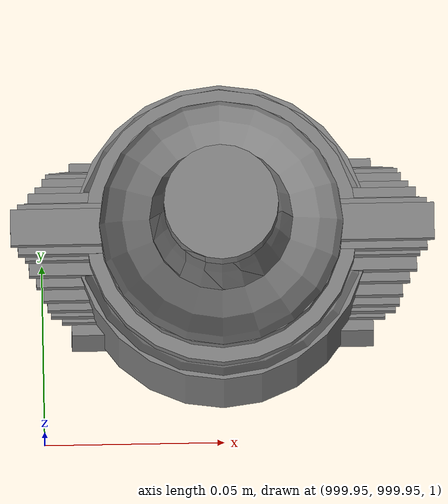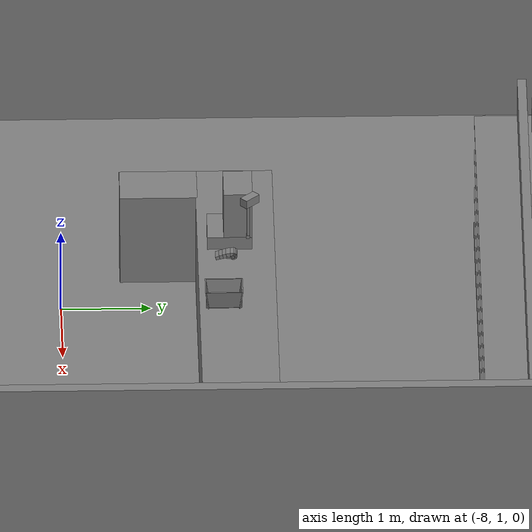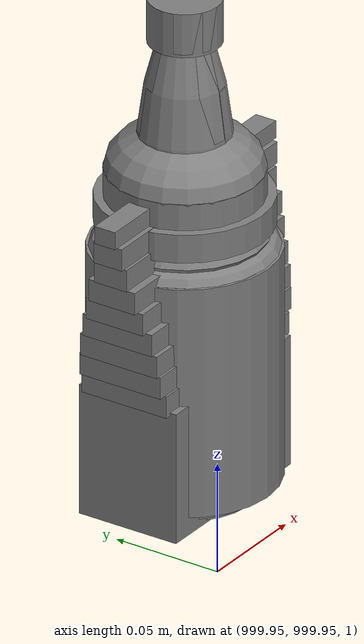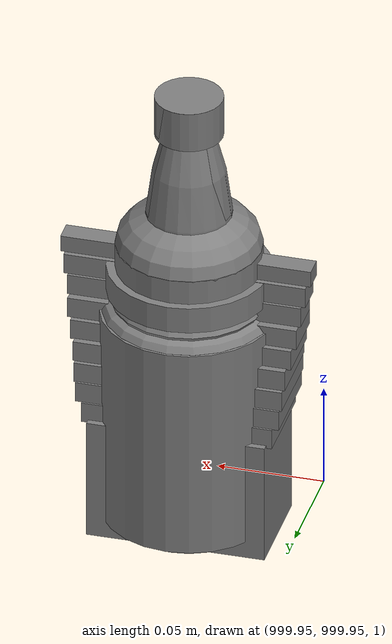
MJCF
<mujoco>
    <option gravity="0.000000000 0.000000000 -9.810000420" timestep="0.0166666" integrator="implicitfast" density="1.225" viscosity="1.8000001e-05" noslip_iterations="10" iterations="100" sdf_iterations="50">
        <flag multiccd="disable"/>
    </option>
    <size memory="1000M"/>
    <compiler coordinate="local"/>
    <worldbody>
        <light cutoff="30" pos="0 1 1" dir="0 -1 -2"/>
        <light cutoff="30" pos="0 -1 1" dir="0 1 -2"/>
        <body pos="-2.436573029 6.404376507 0.137849092" euler="0.000000000 0.000000000 0.000000000" name="openloong_gripper_2f85_fix_base_usda_shoppingtrolley_01">
            <geom contype="1" conaffinity="1" density="1000" type="box" material="" rgba="0.500000000 0.500000000 0.500000000 1.000000000" solimp="0.899999976 0.949999988 0.001000000" friction="1.000000000 0.005000000 0.000100000" solref="0.020000000 1.000000000" margin="0" condim="3" group="0" pos="-0.169898406 -0.178061336 0.864131629" quat="0.916343808 -0.400392294 -0.000000045 0.000000030" size="0.017999999 0.022499999 0.089999996" name="openloong_gripper_2f85_fix_base_usda_geom_C185773D_5855_4625_8ECE_F9FDAADED34E"/>
            <geom contype="1" conaffinity="1" density="1000" type="box" material="" rgba="0.500000000 0.500000000 0.500000000 1.000000000" solimp="0.899999976 0.949999988 0.001000000" friction="1.000000000 0.005000000 0.000100000" solref="0.020000000 1.000000000" margin="0" condim="3" group="0" pos="-0.107458733 0.238907143 0.911498845" quat="0.634576976 0.622505128 -0.330067992 -0.317575932" size="0.017999999 0.022499999 0.035999998" name="openloong_gripper_2f85_fix_base_usda_geom_F8CCBE20_F344_44FE_AD1B_4C6D55194164"/>
            <geom contype="1" conaffinity="1" density="1000" type="box" material="" rgba="0.500000000 0.500000000 0.500000000 1.000000000" solimp="0.899999976 0.949999988 0.001000000" friction="1.000000000 0.005000000 0.000100000" solref="0.020000000 1.000000000" margin="0" condim="3" group="0" pos="-0.005004787 0.248085022 0.912686050" quat="1.000000000 0.000000000 0.000000000 0.000000000" size="0.107999995 0.022499999 0.022499999" name="openloong_gripper_2f85_fix_base_usda_geom_6F5FFE16_B70B_458E_A86C_0AC5A863E794"/>
            <geom contype="1" conaffinity="1" density="1000" type="box" material="" rgba="0.500000000 0.500000000 0.500000000 1.000000000" solimp="0.899999976 0.949999988 0.001000000" friction="1.000000000 0.005000000 0.000100000" solref="0.020000000 1.000000000" margin="0" condim="3" group="0" pos="0.131482959 -0.182533979 0.598989725" quat="0.996607125 0.055331629 0.059003670 0.015205893" size="0.013499999 0.287999988 0.053999998" name="openloong_gripper_2f85_fix_base_usda_geom_4646CCCE_ED81_4951_922E_971CE0FCEAB9"/>
            <geom contype="1" conaffinity="1" density="1000" type="box" material="" rgba="0.500000000 0.500000000 0.500000000 1.000000000" solimp="0.899999976 0.949999988 0.001000000" friction="1.000000000 0.005000000 0.000100000" solref="0.020000000 1.000000000" margin="0" condim="3" group="0" pos="-0.000005364 0.100332208 0.734785020" quat="0.999668717 0.025737956 -0.000000010 0.000000000" size="0.135000005 0.019800000 0.152999997" name="openloong_gripper_2f85_fix_base_usda_geom_376ED7FA_C497_4CEC_ABAA_A1DBD636F92D"/>
            <geom contype="1" conaffinity="1" density="1000" type="box" material="" rgba="0.500000000 0.500000000 0.500000000 1.000000000" solimp="0.899999976 0.949999988 0.001000000" friction="1.000000000 0.005000000 0.000100000" solref="0.020000000 1.000000000" margin="0" condim="3" group="0" pos="-0.126757339 -0.182533979 0.598989725" quat="0.996607184 0.055331606 -0.059003651 -0.015205891" size="0.013499999 0.287999988 0.053999998" name="openloong_gripper_2f85_fix_base_usda_geom_236F6140_2BDF_44BE_A091_BC9D3269E2CF"/>
            <geom contype="1" conaffinity="1" density="1000" type="box" material="" rgba="0.500000000 0.500000000 0.500000000 1.000000000" solimp="0.899999976 0.949999988 0.001000000" friction="1.000000000 0.005000000 0.000100000" solref="0.020000000 1.000000000" margin="0" condim="3" group="0" pos="-0.134013891 0.200098798 0.912192523" quat="0.694057047 0.679413557 -0.172947660 -0.163618833" size="0.017999999 0.022499999 0.035999998" name="openloong_gripper_2f85_fix_base_usda_geom_BCA843DE_8DBA_44D9_86D2_A299B5F4BC3A"/>
            <geom contype="1" conaffinity="1" density="1000" type="box" material="" rgba="0.500000000 0.500000000 0.500000000 1.000000000" solimp="0.899999976 0.949999988 0.001000000" friction="1.000000000 0.005000000 0.000100000" solref="0.020000000 1.000000000" margin="0" condim="3" group="0" pos="0.141839072 -0.191051379 0.702451229" quat="0.997147262 0.056065105 0.045779929 0.021407485" size="0.013499999 0.287999988 0.053999998" name="openloong_gripper_2f85_fix_base_usda_geom_B84FFBE7_DB1E_4E6F_95DA_10DFB6BE2B59"/>
            <geom contype="1" conaffinity="1" density="1000" type="box" material="" rgba="0.500000000 0.500000000 0.500000000 1.000000000" solimp="0.899999976 0.949999988 0.001000000" friction="1.000000000 0.005000000 0.000100000" solref="0.020000000 1.000000000" margin="0" condim="3" group="0" pos="-0.135714188 -0.191051379 0.694841146" quat="0.997147322 0.056064609 -0.045779683 -0.021407485" size="0.013499999 0.287999988 0.053999998" name="openloong_gripper_2f85_fix_base_usda_geom_CC4526F3_D936_4F1C_8880_43F9F8341E63"/>
            <geom contype="1" conaffinity="1" density="1000" type="box" material="" rgba="0.500000000 0.500000000 0.500000000 1.000000000" solimp="0.899999976 0.949999988 0.001000000" friction="1.000000000 0.005000000 0.000100000" solref="0.020000000 1.000000000" margin="0" condim="3" group="0" pos="-0.000004721 -0.174527690 0.560063601" quat="0.996704638 0.081116498 -0.000000004 0.000000000" size="0.126000002 0.287999988 0.009000000" name="openloong_gripper_2f85_fix_base_usda_geom_BE2A9D53_89FD_4385_B9BB_744C4B746513"/>
            <geom contype="1" conaffinity="1" density="1000" type="box" material="" rgba="0.500000000 0.500000000 0.500000000 1.000000000" solimp="0.899999976 0.949999988 0.001000000" friction="1.000000000 0.005000000 0.000100000" solref="0.020000000 1.000000000" margin="0" condim="3" group="0" pos="0.134013891 0.200098798 0.912192523" quat="0.692574680 -0.680924535 -0.166899428 0.169783980" size="0.017999999 0.022499999 0.035999998" name="openloong_gripper_2f85_fix_base_usda_geom_16619333_9996_489B_A6FE_37DC64296DE8"/>
            <geom contype="1" conaffinity="1" density="1000" type="box" material="" rgba="0.500000000 0.500000000 0.500000000 1.000000000" solimp="0.899999976 0.949999988 0.001000000" friction="1.000000000 0.005000000 0.000100000" solref="0.020000000 1.000000000" margin="0" condim="3" group="0" pos="-0.012634277 -0.174527690 -0.088243507" quat="1.000000000 0.000000000 -0.000000004 0.000000000" size="0.135000005 0.287999988 0.044999998" name="openloong_gripper_2f85_fix_base_usda_geom_F54E6249_0EE0_43A7_85CB_4161FB1AE758"/>
            <geom contype="1" conaffinity="1" density="1000" type="box" material="" rgba="0.500000000 0.500000000 0.500000000 1.000000000" solimp="0.899999976 0.949999988 0.001000000" friction="1.000000000 0.005000000 0.000100000" solref="0.020000000 1.000000000" margin="0" condim="3" group="0" pos="-0.142927840 -0.199506134 0.784674108" quat="0.998421252 0.016904408 -0.027109101 -0.046199299" size="0.013499999 0.305999994 0.063000001" name="openloong_gripper_2f85_fix_base_usda_geom_94B563D4_3377_45E4_A56C_BEA1736C2189"/>
            <geom contype="1" conaffinity="1" density="1000" type="box" material="" rgba="0.500000000 0.500000000 0.500000000 1.000000000" solimp="0.899999976 0.949999988 0.001000000" friction="1.000000000 0.005000000 0.000100000" solref="0.020000000 1.000000000" margin="0" condim="3" group="0" pos="-0.169898406 -0.043119621 0.915120542" quat="0.687021017 0.726584017 -0.005590606 -0.006832919" size="0.017999999 0.022499999 0.089999996" name="openloong_gripper_2f85_fix_base_usda_geom_DDA84C7A_ECDE_42EA_B61A_363B1E1EDD3E"/>
            <geom contype="1" conaffinity="1" density="1000" type="box" material="" rgba="0.500000000 0.500000000 0.500000000 1.000000000" solimp="0.899999976 0.949999988 0.001000000" friction="1.000000000 0.005000000 0.000100000" solref="0.020000000 1.000000000" margin="0" condim="3" group="0" pos="-0.000006008 -0.484932661 0.670727849" quat="0.997585475 0.069449045 -0.000000004 -0.000000089" size="0.179999992 0.013499999 0.170999989" name="openloong_gripper_2f85_fix_base_usda_geom_DD01422D_23F4_4897_A79A_011634582D28"/>
            <geom contype="1" conaffinity="1" density="1000" type="box" material="" rgba="0.500000000 0.500000000 0.500000000 1.000000000" solimp="0.899999976 0.949999988 0.001000000" friction="1.000000000 0.005000000 0.000100000" solref="0.020000000 1.000000000" margin="0" condim="3" group="0" pos="0.160832971 0.103427693 0.910528183" quat="0.711112797 -0.700149298 -0.042821646 0.047705106" size="0.017999999 0.022499999 0.071999997" name="openloong_gripper_2f85_fix_base_usda_geom_90BEB926_95AB_4A3A_9C60_B66A718B98BB"/>
            <geom contype="1" conaffinity="1" density="1000" type="box" material="" rgba="0.500000000 0.500000000 0.500000000 1.000000000" solimp="0.899999976 0.949999988 0.001000000" friction="1.000000000 0.005000000 0.000100000" solref="0.020000000 1.000000000" margin="0" condim="3" group="0" pos="-0.160832763 0.103427693 0.910528183" quat="0.711469591 0.699786782 -0.048386075 -0.042050660" size="0.017999999 0.022499999 0.071999997" name="openloong_gripper_2f85_fix_base_usda_geom_6CBF74B3_C4BD_4924_9B67_64E94B62F0D1"/>
            <geom contype="1" conaffinity="1" density="1000" type="box" material="" rgba="0.500000000 0.500000000 0.500000000 1.000000000" solimp="0.899999976 0.949999988 0.001000000" friction="1.000000000 0.005000000 0.000100000" solref="0.020000000 1.000000000" margin="0" condim="3" group="0" pos="0.169898629 -0.178061336 0.864131629" quat="0.916343808 -0.400392294 -0.000000045 0.000000030" size="0.017999999 0.022499999 0.089999996" name="openloong_gripper_2f85_fix_base_usda_geom_4AACD471_991C_4C55_8A1D_5D520FB9F804"/>
            <geom contype="1" conaffinity="1" density="1000" type="box" material="" rgba="0.500000000 0.500000000 0.500000000 1.000000000" solimp="0.899999976 0.949999988 0.001000000" friction="1.000000000 0.005000000 0.000100000" solref="0.020000000 1.000000000" margin="0" condim="3" group="0" pos="0.103667587 0.233050480 0.912927270" quat="0.634205043 -0.622199059 -0.324503720 0.324576139" size="0.017999999 0.022499999 0.035999998" name="openloong_gripper_2f85_fix_base_usda_geom_4B7826AD_18B7_44DD_9E37_025C1F6D93BB"/>
            <geom contype="1" conaffinity="1" density="1000" type="box" material="" rgba="0.500000000 0.500000000 0.500000000 1.000000000" solimp="0.899999976 0.949999988 0.001000000" friction="1.000000000 0.005000000 0.000100000" solref="0.020000000 1.000000000" margin="0" condim="3" group="0" pos="0.169898629 -0.043119621 0.915120542" quat="0.687029123 -0.726576388 -0.006509603 0.005963952" size="0.017999999 0.022499999 0.089999996" name="openloong_gripper_2f85_fix_base_usda_geom_DA256968_7097_4369_9841_1ECFF30DCC5D"/>
            <geom contype="1" conaffinity="1" density="1000" type="box" material="" rgba="0.500000000 0.500000000 0.500000000 1.000000000" solimp="0.899999976 0.949999988 0.001000000" friction="1.000000000 0.005000000 0.000100000" solref="0.020000000 1.000000000" margin="0" condim="3" group="0" pos="0.148195267 -0.199506566 0.782808602" quat="0.998808920 0.017156634 0.026950166 0.036880098" size="0.013499999 0.305999994 0.063000001" name="openloong_gripper_2f85_fix_base_usda_geom_16B6C74E_CF62_4D5D_98FE_AE0BCD98DB8B"/>
            <freejoint name="openloong_gripper_2f85_fix_base_usda_shoppingtrolley_01_joint"/>
            <site size="0.005000000 0.005000000 0.005000000" rgba="0.500000000 0.500000000 0.500000000 1.000000000" pos="0.000000000 0.000000000 0.000000000" quat="1.000000000 0.000000000 0.000000000 0.000000000" group="0" type="sphere" name="openloong_gripper_2f85_fix_base_usda_shoppingtrolley_01"/>
        </body>
        <body pos="1000.000000000 1000.000000000 1.000000000" euler="0.000000000 0.000000000 0.000000000" name="openloong_gripper_2f85_fix_base_usda_bottle_red">
            <geom contype="1" conaffinity="1" density="1000" type="ellipsoid" material="" rgba="0.500000000 0.500000000 0.500000000 1.000000000" solimp="0.899999976 0.949999988 0.001000000" friction="1.000000000 0.005000000 0.000100000" solref="0.020000000 1.000000000" margin="0" condim="3" group="0" pos="0.000000000 0.000000000 0.144284487" quat="1.000000000 0.000000000 0.000000000 0.000000000" size="0.021000000 0.021000000 0.079999998" name="openloong_gripper_2f85_fix_base_usda_geom_88E947D4_CEDB_46EE_AA86_A423E6E6F3AC"/>
            <geom contype="1" conaffinity="1" density="1000" type="cylinder" material="" rgba="0.500000000 0.500000000 0.500000000 1.000000000" solimp="0.899999976 0.949999988 0.001000000" friction="1.000000000 0.005000000 0.000100000" solref="0.020000000 1.000000000" margin="0" condim="3" group="0" pos="0.000000000 0.000000000 0.220618963" quat="1.000000000 0.000000000 0.000000000 0.000000000" size="0.016000001 0.010000000 1.000000000" name="openloong_gripper_2f85_fix_base_usda_geom_F54C3974_8D15_440A_B923_5DA35C1A1688"/>
            <geom contype="1" conaffinity="1" density="1000" type="ellipsoid" material="" rgba="0.500000000 0.500000000 0.500000000 1.000000000" solimp="0.899999976 0.949999988 0.001000000" friction="1.000000000 0.005000000 0.000100000" solref="0.020000000 1.000000000" margin="0" condim="3" group="0" pos="0.000000000 0.000000000 0.118945479" quat="1.000000000 0.000000000 0.000000000 0.000000000" size="0.030999999 0.030999999 0.029999999" name="openloong_gripper_2f85_fix_base_usda_geom_9627272D_6C69_4A43_8302_7759E6548FD6"/>
            <geom contype="1" conaffinity="1" density="1000" type="box" material="" rgba="0.500000000 0.500000000 0.500000000 1.000000000" solimp="0.899999976 0.949999988 0.001000000" friction="1.000000000 0.005000000 0.000100000" solref="0.020000000 1.000000000" margin="0" condim="3" group="0" pos="0.000000000 0.000000000 0.002189159" quat="1.000000000 0.000000000 0.000000000 0.000000000" size="0.020000000 0.020000000 0.003000000" name="openloong_gripper_2f85_fix_base_usda_geom_439C426E_8AB5_4E6C_A998_704875875D72"/>
            <geom contype="1" conaffinity="1" density="1000" type="cylinder" material="" rgba="0.500000000 0.500000000 0.500000000 1.000000000" solimp="0.899999976 0.949999988 0.001000000" friction="1.000000000 0.005000000 0.000100000" solref="0.020000000 1.000000000" margin="0" condim="3" group="0" pos="0.000000000 -0.000366211 0.060884237" quat="1.000000000 0.000000000 0.000000000 0.000000000" size="0.030999999 0.057999998 1.000000000" name="openloong_gripper_2f85_fix_base_usda_geom_4BD4FA60_CA5D_440E_B56A_D0BCFE651C02"/>
            <freejoint name="openloong_gripper_2f85_fix_base_usda_bottle_red_joint"/>
            <site size="0.005000000 0.005000000 0.005000000" rgba="0.500000000 0.500000000 0.500000000 1.000000000" pos="0.000000000 0.000000000 0.000000000" quat="0.999961913 0.008726535 0.000000000 0.000000000" group="0" type="sphere" name="openloong_gripper_2f85_fix_base_usda_bottle_redsite"/>
        </body>
        <body pos="-2.318005085 6.317743778 1.716063142" euler="77.585502625 -4.300077915 -44.447917938" mocap="true" name="spotlight6_SpotLight"/>
        <body pos="1000.000000000 1000.000000000 1.000000000" euler="0.000000000 0.000000000 0.000000000" name="openloong_gripper_2f85_fix_base_usda_bottle_blue">
            <geom contype="1" conaffinity="1" density="1000" type="ellipsoid" material="" rgba="0.500000000 0.500000000 0.500000000 1.000000000" solimp="0.899999976 0.949999988 0.001000000" friction="1.000000000 0.005000000 0.000100000" solref="0.020000000 1.000000000" margin="0" condim="3" group="0" pos="0.000000000 0.000000000 0.118920922" quat="1.000000000 0.000000000 0.000000000 0.000000000" size="0.030999999 0.030999999 0.029999999" name="openloong_gripper_2f85_fix_base_usda_geom_3377EB75_1E33_4E5A_A2C8_A320997EE799"/>
            <geom contype="1" conaffinity="1" density="1000" type="box" material="" rgba="0.500000000 0.500000000 0.500000000 1.000000000" solimp="0.899999976 0.949999988 0.001000000" friction="1.000000000 0.005000000 0.000100000" solref="0.020000000 1.000000000" margin="0" condim="3" group="0" pos="0.000000000 0.000000000 0.002164602" quat="1.000000000 0.000000000 0.000000000 0.000000000" size="0.020000000 0.020000000 0.003000000" name="openloong_gripper_2f85_fix_base_usda_geom_988FFF4B_34F9_464F_9127_62611810FC44"/>
            <geom contype="1" conaffinity="1" density="1000" type="cylinder" material="" rgba="0.500000000 0.500000000 0.500000000 1.000000000" solimp="0.899999976 0.949999988 0.001000000" friction="1.000000000 0.005000000 0.000100000" solref="0.020000000 1.000000000" margin="0" condim="3" group="0" pos="0.000000000 -0.000366211 0.060859680" quat="1.000000000 0.000000000 0.000000000 0.000000000" size="0.030999999 0.057999998 1.000000000" name="openloong_gripper_2f85_fix_base_usda_geom_D83E7B3A_DFAA_434A_AE4C_CDC51E788F89"/>
            <geom contype="1" conaffinity="1" density="1000" type="cylinder" material="" rgba="0.500000000 0.500000000 0.500000000 1.000000000" solimp="0.899999976 0.949999988 0.001000000" friction="1.000000000 0.005000000 0.000100000" solref="0.020000000 1.000000000" margin="0" condim="3" group="0" pos="0.000000000 0.000000000 0.220594406" quat="1.000000000 0.000000000 0.000000000 0.000000000" size="0.016000001 0.010000000 1.000000000" name="openloong_gripper_2f85_fix_base_usda_geom_CAE41944_E2DB_4341_AA74_2936B10D0E45"/>
            <geom contype="1" conaffinity="1" density="1000" type="ellipsoid" material="" rgba="0.500000000 0.500000000 0.500000000 1.000000000" solimp="0.899999976 0.949999988 0.001000000" friction="1.000000000 0.005000000 0.000100000" solref="0.020000000 1.000000000" margin="0" condim="3" group="0" pos="0.000000000 0.000000000 0.144259930" quat="1.000000000 0.000000000 0.000000000 0.000000000" size="0.021000000 0.021000000 0.079999998" name="openloong_gripper_2f85_fix_base_usda_geom_70709434_810F_48E5_AF86_0E2576573B42"/>
            <freejoint name="openloong_gripper_2f85_fix_base_usda_bottle_blue_joint"/>
            <site size="0.005000000 0.005000000 0.005000000" rgba="0.500000000 0.500000000 0.500000000 1.000000000" pos="0.000000000 0.000000000 0.000000000" quat="0.999961913 0.008726535 0.000000000 0.000000000" group="0" type="sphere" name="openloong_gripper_2f85_fix_base_usda_bottle_bluesite"/>
        </body>
        <body pos="1000.000000000 1000.000000000 1.000000000" euler="0.000000000 0.000000000 0.000000000" name="openloong_gripper_2f85_fix_base_usda_jar_01">
            <geom contype="1" conaffinity="1" density="1000" type="box" material="" rgba="0.500000000 0.500000000 0.500000000 1.000000000" solimp="0.899999976 0.949999988 0.001000000" friction="1.000000000 0.005000000 0.000100000" solref="0.020000000 1.000000000" margin="0" condim="3" group="0" pos="0.000000000 0.000000000 0.006158113" quat="1.000000000 0.000000000 0.000000000 0.000000000" size="0.020000000 0.020000000 0.005000000" name="openloong_gripper_2f85_fix_base_usda_geom_54EE365A_44D5_4067_B863_26EC02DB9ABC"/>
            <geom contype="1" conaffinity="1" density="1000" type="cylinder" material="" rgba="0.500000000 0.500000000 0.500000000 1.000000000" solimp="0.899999976 0.949999988 0.001000000" friction="1.000000000 0.005000000 0.000100000" solref="0.020000000 1.000000000" margin="0" condim="3" group="0" pos="0.000000000 0.000000000 0.062744498" quat="1.000000000 0.000000000 0.000000000 0.000000000" size="0.041000001 0.052999999 1.000000000" name="openloong_gripper_2f85_fix_base_usda_geom_BCA20582_B804_4EEF_AD55_D25CB0CF0E10"/>
            <geom contype="1" conaffinity="1" density="1000" type="ellipsoid" material="" rgba="0.500000000 0.500000000 0.500000000 1.000000000" solimp="0.899999976 0.949999988 0.001000000" friction="1.000000000 0.005000000 0.000100000" solref="0.020000000 1.000000000" margin="0" condim="3" group="0" pos="0.000000000 0.000000000 0.122252703" quat="1.000000000 0.000000000 0.000000000 0.000000000" size="0.035999998 0.035999998 0.010000000" name="openloong_gripper_2f85_fix_base_usda_geom_34736000_72C1_4768_995D_E0C35909422E"/>
            <geom contype="1" conaffinity="1" density="1000" type="cylinder" material="" rgba="0.500000000 0.500000000 0.500000000 1.000000000" solimp="0.899999976 0.949999988 0.001000000" friction="1.000000000 0.005000000 0.000100000" solref="0.020000000 1.000000000" margin="0" condim="3" group="0" pos="0.000000000 0.000000000 0.015747190" quat="1.000000000 0.000000000 0.000000000 0.000000000" size="0.035000000 0.010000000 1.000000000" name="openloong_gripper_2f85_fix_base_usda_geom_3C03EE16_1814_456D_A39A_37935C486D22"/>
            <geom contype="1" conaffinity="1" density="1000" type="ellipsoid" material="" rgba="0.500000000 0.500000000 0.500000000 1.000000000" solimp="0.899999976 0.949999988 0.001000000" friction="1.000000000 0.005000000 0.000100000" solref="0.020000000 1.000000000" margin="0" condim="3" group="0" pos="0.000000000 0.000000000 0.115815401" quat="1.000000000 0.000000000 0.000000000 0.000000000" size="0.039999999 0.039999999 0.010000000" name="openloong_gripper_2f85_fix_base_usda_geom_0A1F38D0_0B46_48B5_A976_86EEB6E0B4A1"/>
            <geom contype="1" conaffinity="1" density="1000" type="cylinder" material="" rgba="0.500000000 0.500000000 0.500000000 1.000000000" solimp="0.899999976 0.949999988 0.001000000" friction="1.000000000 0.005000000 0.000100000" solref="0.020000000 1.000000000" margin="0" condim="3" group="0" pos="0.000000000 0.000000000 0.133183479" quat="1.000000000 0.000000000 0.000000000 0.000000000" size="0.037999999 0.006500000 1.000000000" name="openloong_gripper_2f85_fix_base_usda_geom_E76A1CC3_94C7_4FBA_8E36_3A4F268563A5"/>
            <freejoint name="openloong_gripper_2f85_fix_base_usda_jar_01_joint"/>
            <site size="0.005000000 0.005000000 0.005000000" rgba="0.500000000 0.500000000 0.500000000 1.000000000" pos="0.000000000 0.000000000 0.000000000" quat="1.000000000 0.000000000 0.000000000 0.000000000" group="0" type="sphere" name="openloong_gripper_2f85_fix_base_usda_jar_01site"/>
        </body>
        <body pos="1000.000000000 1000.000000000 1.000000000" euler="0.000000000 0.000000000 0.000000000" name="openloong_gripper_2f85_fix_base_usda_salt">
            <geom contype="1" conaffinity="1" density="1000" type="box" material="" rgba="0.500000000 0.500000000 0.500000000 1.000000000" solimp="0.899999976 0.949999988 0.001000000" friction="1.000000000 0.005000000 0.000100000" solref="0.020000000 1.000000000" margin="0" condim="3" group="0" pos="0.000305176 0.000000000 0.084862232" quat="1.000000000 0.000000000 0.000000000 0.000000000" size="0.048999999 0.018999999 0.005000000" name="openloong_gripper_2f85_fix_base_usda_geom_7A8CD7A4_2EB5_4BEA_B4A8_B9373090E351"/>
            <geom contype="1" conaffinity="1" density="1000" type="box" material="" rgba="0.500000000 0.500000000 0.500000000 1.000000000" solimp="0.899999976 0.949999988 0.001000000" friction="1.000000000 0.005000000 0.000100000" solref="0.020000000 1.000000000" margin="0" condim="3" group="0" pos="0.000305176 0.000000000 0.104564309" quat="1.000000000 0.000000000 0.000000000 0.000000000" size="0.052000001 0.014000000 0.005000000" name="openloong_gripper_2f85_fix_base_usda_geom_73E6C6F4_E321_425E_B1B2_D538E333F143"/>
            <geom contype="1" conaffinity="1" density="1000" type="box" material="" rgba="0.500000000 0.500000000 0.500000000 1.000000000" solimp="0.899999976 0.949999988 0.001000000" friction="1.000000000 0.005000000 0.000100000" solref="0.020000000 1.000000000" margin="0" condim="3" group="0" pos="0.000305176 0.000000000 0.114487171" quat="1.000000000 0.000000000 0.000000000 0.000000000" size="0.054000001 0.011500000 0.005000000" name="openloong_gripper_2f85_fix_base_usda_geom_65DD6784_4625_4B0B_ABED_FED5DE82D31F"/>
            <geom contype="1" conaffinity="1" density="1000" type="box" material="" rgba="0.500000000 0.500000000 0.500000000 1.000000000" solimp="0.899999976 0.949999988 0.001000000" friction="1.000000000 0.005000000 0.000100000" solref="0.020000000 1.000000000" margin="0" condim="3" group="0" pos="0.000305176 0.000000000 0.075103164" quat="1.000000000 0.000000000 0.000000000 0.000000000" size="0.048000000 0.020000000 0.005000000" name="openloong_gripper_2f85_fix_base_usda_geom_E11F6E25_2583_46E6_B08D_647E6D0B4B42"/>
            <geom contype="1" conaffinity="1" density="1000" type="box" material="" rgba="0.500000000 0.500000000 0.500000000 1.000000000" solimp="0.899999976 0.949999988 0.001000000" friction="1.000000000 0.005000000 0.000100000" solref="0.020000000 1.000000000" margin="0" condim="3" group="0" pos="0.000305176 0.000000000 0.134892464" quat="1.000000000 0.000000000 0.000000000 0.000000000" size="0.057000000 0.007000000 0.005000000" name="openloong_gripper_2f85_fix_base_usda_geom_827FECC1_003E_4B51_93C4_5B0D39E53C57"/>
            <geom contype="1" conaffinity="1" density="1000" type="box" material="" rgba="0.500000000 0.500000000 0.500000000 1.000000000" solimp="0.899999976 0.949999988 0.001000000" friction="1.000000000 0.005000000 0.000100000" solref="0.020000000 1.000000000" margin="0" condim="3" group="0" pos="0.000305176 0.000000000 0.094920278" quat="1.000000000 0.000000000 0.000000000 0.000000000" size="0.050000001 0.017000001 0.005000000" name="openloong_gripper_2f85_fix_base_usda_geom_18316E2C_F736_4D74_B475_12F4C0008A93"/>
            <geom contype="1" conaffinity="1" density="1000" type="box" material="" rgba="0.500000000 0.500000000 0.500000000 1.000000000" solimp="0.899999976 0.949999988 0.001000000" friction="1.000000000 0.005000000 0.000100000" solref="0.020000000 1.000000000" margin="0" condim="3" group="0" pos="0.000305176 0.000000000 0.065204859" quat="1.000000000 0.000000000 0.000000000 0.000000000" size="0.045000002 0.021000000 0.005000000" name="openloong_gripper_2f85_fix_base_usda_geom_0A1D4DAF_F10E_4DCB_AD8E_9459997DA1C8"/>
            <geom contype="1" conaffinity="1" density="1000" type="box" material="" rgba="0.500000000 0.500000000 0.500000000 1.000000000" solimp="0.899999976 0.949999988 0.001000000" friction="1.000000000 0.005000000 0.000100000" solref="0.020000000 1.000000000" margin="0" condim="3" group="0" pos="0.000305176 0.000000000 0.144135714" quat="1.000000000 0.000000000 0.000000000 0.000000000" size="0.059000000 0.005000000 0.004000000" name="openloong_gripper_2f85_fix_base_usda_geom_739E18FB_30B0_462C_884D_3D3020EEB1F6"/>
            <geom contype="1" conaffinity="1" density="1000" type="box" material="" rgba="0.500000000 0.500000000 0.500000000 1.000000000" solimp="0.899999976 0.949999988 0.001000000" friction="1.000000000 0.005000000 0.000100000" solref="0.020000000 1.000000000" margin="0" condim="3" group="0" pos="0.000000000 0.000000000 0.031593561" quat="1.000000000 0.000000000 0.000000000 0.000000000" size="0.041999999 0.024000000 0.029999999" name="openloong_gripper_2f85_fix_base_usda_geom_2FB95B09_1261_49C8_B9D9_A4711901A044"/>
            <geom contype="1" conaffinity="1" density="1000" type="box" material="" rgba="0.500000000 0.500000000 0.500000000 1.000000000" solimp="0.899999976 0.949999988 0.001000000" friction="1.000000000 0.005000000 0.000100000" solref="0.020000000 1.000000000" margin="0" condim="3" group="0" pos="0.000305176 0.000000000 0.124608755" quat="1.000000000 0.000000000 0.000000000 0.000000000" size="0.055000000 0.008000000 0.005000000" name="openloong_gripper_2f85_fix_base_usda_geom_810E952F_BD44_4DA6_92F3_717F8134C558"/>
            <freejoint name="openloong_gripper_2f85_fix_base_usda_salt_joint"/>
            <site size="0.005000000 0.005000000 0.005000000" rgba="0.500000000 0.500000000 0.500000000 1.000000000" pos="0.000000000 0.000000000 0.000000000" quat="1.000000000 0.000000000 0.000000000 0.000000000" group="0" type="sphere" name="openloong_gripper_2f85_fix_base_usda_saltsite"/>
        </body>
        <body pos="-2.254847765 6.095495224 1.758548856" euler="121.040588379 2.073225260 23.732980728" mocap="true" name="spotlight3_SpotLight"/>
        <body pos="-2.312985897 6.140238285 1.810317159" euler="147.051177979 -14.727632523 -167.725936890" mocap="true" name="spotlight2_SpotLight"/>
        <body pos="1000.000000000 1000.000000000 1.000000000" euler="0.000000000 0.000000000 0.000000000" name="openloong_gripper_2f85_fix_base_usda_can">
            <geom contype="1" conaffinity="1" density="1000" type="cylinder" material="" rgba="0.500000000 0.500000000 0.500000000 1.000000000" solimp="0.899999976 0.949999988 0.001000000" friction="1.000000000 0.005000000 0.000100000" solref="0.020000000 1.000000000" margin="0" condim="3" group="0" pos="0.000000000 0.000000000 0.079676986" quat="1.000000000 0.000000000 0.000000000 0.000000000" size="0.034000002 0.071999997 1.000000000" name="openloong_gripper_2f85_fix_base_usda_geom_01ED0AB3_D805_40A3_BE94_070333B5AE26"/>
            <geom contype="1" conaffinity="1" density="1000" type="ellipsoid" material="" rgba="0.500000000 0.500000000 0.500000000 1.000000000" solimp="0.899999976 0.949999988 0.001000000" friction="1.000000000 0.005000000 0.000100000" solref="0.020000000 1.000000000" margin="0" condim="3" group="0" pos="0.000000000 0.000000000 0.151854277" quat="1.000000000 0.000000000 0.000000000 0.000000000" size="0.034000002 0.034000002 0.020000000" name="openloong_gripper_2f85_fix_base_usda_geom_D9741F2E_9DE9_44CB_8C97_DE562099CE08"/>
            <geom contype="1" conaffinity="1" density="1000" type="box" material="" rgba="0.500000000 0.500000000 0.500000000 1.000000000" solimp="0.899999976 0.949999988 0.001000000" friction="1.000000000 0.005000000 0.000100000" solref="0.020000000 1.000000000" margin="0" condim="3" group="0" pos="0.000000000 0.000000000 0.004777670" quat="1.000000000 0.000000000 0.000000000 0.000000000" size="0.020000000 0.020000000 0.005000000" name="openloong_gripper_2f85_fix_base_usda_geom_92C51F17_DBFC_44A2_B205_20A8BEB7B3A4"/>
            <freejoint name="openloong_gripper_2f85_fix_base_usda_can_joint"/>
            <site size="0.005000000 0.005000000 0.005000000" rgba="0.500000000 0.500000000 0.500000000 1.000000000" pos="0.000000000 0.000000000 0.000000000" quat="1.000000000 0.000000000 0.000000000 0.000000000" group="0" type="sphere" name="openloong_gripper_2f85_fix_base_usda_cansite"/>
        </body>
        <body pos="0.000000000 0.000000000 0.000000000" euler="0.000000000 0.000000000 0.000000000" name=" Static Objects_ Static Objects">
            <geom contype="1" conaffinity="1" density="1000" type="box" material="" rgba="0.500000000 0.500000000 0.500000000 1.000000000" solimp="0.899999976 0.949999988 0.001000000" friction="1.000000000 0.005000000 0.000100000" solref="0.020000000 1.000000000" margin="0" condim="3" group="0" pos="-3.101639986 6.150595188 1.018643856" quat="1.000000000 0.000000000 0.000000000 0.000000000" size="0.050000001 0.579999983 1.019999981" name=" Static Objects_geom_2A5A6D77_7F6E_4E46_95C6_585A1820726A"/>
            <geom contype="1" conaffinity="1" density="1000" type="box" material="" rgba="0.500000000 0.500000000 0.500000000 1.000000000" solimp="0.899999976 0.949999988 0.001000000" friction="1.000000000 0.005000000 0.000100000" solref="0.020000000 1.000000000" margin="0" condim="3" group="0" pos="-2.825197220 6.153595448 1.115278244" quat="0.707107067 0.000000000 0.000000000 0.707106471" size="0.550000012 0.239999995 0.025000000" name=" Static Objects_geom_6F1039F7_9A43_4522_A607_E6652DCA319F"/>
            <geom contype="1" conaffinity="1" density="1000" type="box" material="" rgba="0.500000000 0.500000000 0.500000000 1.000000000" solimp="0.899999976 0.949999988 0.001000000" friction="1.000000000 0.005000000 0.000100000" solref="0.020000000 1.000000000" margin="0" condim="3" group="0" pos="-2.825197220 6.153595448 0.097434282" quat="0.707107067 0.000000000 0.000000000 0.707106471" size="0.550000012 0.239999995 0.098999999" name=" Static Objects_geom_1B1FD8F3_62E2_4483_B050_D61A63302CDA"/>
            <geom contype="1" conaffinity="1" density="1000" type="box" material="" rgba="0.500000000 0.500000000 0.500000000 1.000000000" solimp="0.899999976 0.949999988 0.001000000" friction="1.000000000 0.005000000 0.000100000" solref="0.020000000 1.000000000" margin="0" condim="3" group="0" pos="-6.293097973 6.153595448 1.114443064" quat="0.707107067 0.000000000 0.000000000 0.707106471" size="0.529999971 3.134999990 0.025000000" name=" Static Objects_geom_8DD023A4_85A2_4C56_9785_9405D2D9C28A"/>
            <geom contype="1" conaffinity="1" density="1000" type="box" material="" rgba="0.500000000 0.500000000 0.500000000 1.000000000" solimp="0.899999976 0.949999988 0.001000000" friction="1.000000000 0.005000000 0.000100000" solref="0.020000000 1.000000000" margin="0" condim="3" group="0" pos="-6.286010742 6.153595448 0.096129179" quat="0.707107067 0.000000000 0.000000000 0.707106471" size="0.529999971 3.134999990 0.098999999" name=" Static Objects_geom_62BB8F17_DD5A_4634_8488_D7A5A1A0AB2F"/>
            <geom contype="1" conaffinity="1" density="1000" type="box" material="" rgba="0.500000000 0.500000000 0.500000000 1.000000000" solimp="0.899999976 0.949999988 0.001000000" friction="1.000000000 0.005000000 0.000100000" solref="0.020000000 1.000000000" margin="0" condim="3" group="0" pos="-2.825197220 6.153595448 1.563861728" quat="0.707107067 0.000000000 0.000000000 0.707106471" size="0.550000012 0.239999995 0.025000000" name=" Static Objects_geom_5EDD968D_B44D_45A6_BDCE_E9067E8AEE14"/>
            <geom contype="1" conaffinity="1" density="1000" type="box" material="" rgba="0.500000000 0.500000000 0.500000000 1.000000000" solimp="0.899999976 0.949999988 0.001000000" friction="1.000000000 0.005000000 0.000100000" solref="0.020000000 1.000000000" margin="0" condim="3" group="0" pos="-6.311686516 6.153595448 1.018643856" quat="0.707107067 0.000000000 0.000000000 0.707106471" size="0.050000001 3.150000095 1.019999981" name=" Static Objects_geom_CA8FF83D_B1ED_49F5_9632_60DBB5212501"/>
            <geom contype="1" conaffinity="1" density="1000" type="box" material="" rgba="0.500000000 0.500000000 0.500000000 1.000000000" solimp="0.899999976 0.949999988 0.001000000" friction="1.000000000 0.005000000 0.000100000" solref="0.020000000 1.000000000" margin="0" condim="3" group="0" pos="-2.825197220 6.153595448 0.629031777" quat="0.707107067 0.000000000 0.000000000 0.707106471" size="0.550000012 0.239999995 0.025000000" name=" Static Objects_geom_78E9B888_642B_4185_8EE3_22A182C9EDC3"/>
            <geom contype="1" conaffinity="1" density="1000" type="box" material="" rgba="0.500000000 0.500000000 0.500000000 1.000000000" solimp="0.899999976 0.949999988 0.001000000" friction="1.000000000 0.005000000 0.000100000" solref="0.020000000 1.000000000" margin="0" condim="3" group="0" pos="-6.286010742 6.153595448 1.563861728" quat="0.707107067 0.000000000 0.000000000 0.707106471" size="0.529999971 3.134999990 0.025000000" name=" Static Objects_geom_42711A42_D57D_45B8_93AD_C7105F3C39DF"/>
            <geom contype="1" conaffinity="1" density="1000" type="box" material="" rgba="0.500000000 0.500000000 0.500000000 1.000000000" solimp="0.899999976 0.949999988 0.001000000" friction="1.000000000 0.005000000 0.000100000" solref="0.020000000 1.000000000" margin="0" condim="3" group="0" pos="-6.286010742 6.153595448 0.629031777" quat="0.707107067 0.000000000 0.000000000 0.707106471" size="0.529999971 3.134999990 0.025000000" name=" Static Objects_geom_ED9A4D5B_34C8_428D_A0EE_A5C824B26DD0"/>
            <geom contype="1" conaffinity="1" density="1000" type="box" material="" rgba="0.500000000 0.500000000 0.500000000 1.000000000" solimp="0.899999976 0.949999988 0.001000000" friction="1.000000000 0.005000000 0.000100000" solref="0.020000000 1.000000000" margin="0" condim="3" group="0" pos="-7.719123363 2.867671013 1.173410416" quat="1.000000000 0.000000000 0.000000000 0.000000000" size="0.250000000 0.250000000 0.079999998" name=" Static Objects_geom_E4BE5723_A220_408C_BFA5_EE56A1BEF401"/>
            <geom contype="1" conaffinity="1" density="1000" type="box" material="" rgba="0.500000000 0.500000000 0.500000000 1.000000000" solimp="0.899999976 0.949999988 0.001000000" friction="1.000000000 0.005000000 0.000100000" solref="0.020000000 1.000000000" margin="0" condim="3" group="0" pos="-7.408766270 3.088089943 1.776644945" quat="0.928051054 0.000000000 0.000000000 0.372453064" size="0.050000001 0.100000001 0.050000001" name=" Static Objects_geom_3A2EECF2_C58F_4920_9C26_44265CD790C8"/>
            <geom contype="1" conaffinity="1" density="1000" type="box" material="" rgba="0.500000000 0.500000000 0.500000000 1.000000000" solimp="0.899999976 0.949999988 0.001000000" friction="1.000000000 0.005000000 0.000100000" solref="0.020000000 1.000000000" margin="0" condim="3" group="0" pos="-7.719123363 2.958004713 1.530241251" quat="1.000000000 0.000000000 0.000000000 0.000000000" size="0.250000000 0.159999996 0.280000001" name=" Static Objects_geom_02813AF7_AAAA_48BF_AC7F_1E5495A035AC"/>
            <geom contype="1" conaffinity="1" density="1000" type="cylinder" material="" rgba="0.500000000 0.500000000 0.500000000 1.000000000" solimp="0.899999976 0.949999988 0.001000000" friction="1.000000000 0.005000000 0.000100000" solref="0.020000000 1.000000000" margin="0" condim="3" group="0" pos="-7.427312374 3.069516420 1.502544641" quat="0.928051054 0.000000000 0.000000000 0.372453064" size="0.015000000 0.230000004 0.100000001" name=" Static Objects_geom_D15D505E_C592_4761_A29C_327E1471BA54"/>
            <geom contype="1" conaffinity="1" density="1000" type="box" material="" rgba="0.500000000 0.500000000 0.500000000 1.000000000" solimp="0.899999976 0.949999988 0.001000000" friction="1.000000000 0.005000000 0.000100000" solref="0.020000000 1.000000000" margin="0" condim="3" group="0" pos="-7.437745571 3.067511320 1.289965630" quat="1.000000000 0.000000000 0.000000000 0.000000000" size="0.029999999 0.020000000 0.020000000" name=" Static Objects_geom_C130F55D_3C79_4BE2_89B5_46A6E9B2DC6A"/>
            <geom contype="1" conaffinity="1" density="1000" type="box" material="" rgba="0.500000000 0.500000000 0.500000000 1.000000000" solimp="0.899999976 0.949999988 0.001000000" friction="1.000000000 0.005000000 0.000100000" solref="0.020000000 1.000000000" margin="0" condim="3" group="0" pos="-9.058088303 6.434794426 1.209077358" quat="1.000000000 0.000000000 0.000000000 0.000000000" size="0.250000000 0.100000001 0.070000000" name=" Static Objects_geom_4F086053_EAA1_4A9C_BA21_C3E731216FED"/>
            <geom contype="1" conaffinity="1" density="1000" type="box" material="" rgba="0.500000000 0.500000000 0.500000000 1.000000000" solimp="0.899999976 0.949999988 0.001000000" friction="1.000000000 0.005000000 0.000100000" solref="0.020000000 1.000000000" margin="0" condim="3" group="0" pos="-7.886891365 6.459744930 0.352518857" quat="1.000000000 0.000000000 0.000000000 0.000000000" size="1.500000000 0.200000003 0.150000006" name=" Static Objects_geom_7322E45D_376C_4ACC_8CCE_B5922AE0AE3E"/>
            <geom contype="1" conaffinity="1" density="1000" type="box" material="" rgba="0.500000000 0.500000000 0.500000000 1.000000000" solimp="0.899999976 0.949999988 0.001000000" friction="1.000000000 0.005000000 0.000100000" solref="0.020000000 1.000000000" margin="0" condim="3" group="0" pos="-9.237723351 6.464855671 1.209077358" quat="1.000000000 0.000000000 0.000000000 0.000000000" size="0.100000001 0.100000001 0.070000000" name=" Static Objects_geom_7467EB64_938C_49F1_856A_DD4CB86039BF"/>
            <geom contype="1" conaffinity="1" density="1000" type="box" material="" rgba="0.500000000 0.500000000 0.500000000 1.000000000" solimp="0.899999976 0.949999988 0.001000000" friction="1.000000000 0.005000000 0.000100000" solref="0.020000000 1.000000000" margin="0" condim="3" group="0" pos="-6.924745083 6.362090111 1.214329123" quat="1.000000000 0.000000000 0.000000000 0.000000000" size="0.200000003 0.100000001 0.075000003" name=" Static Objects_geom_A4863FA8_7BB5_4351_91DF_4B5A0FBFBD76"/>
            <geom contype="1" conaffinity="1" density="1000" type="box" material="" rgba="0.500000000 0.500000000 0.500000000 1.000000000" solimp="0.899999976 0.949999988 0.001000000" friction="1.000000000 0.005000000 0.000100000" solref="0.020000000 1.000000000" margin="0" condim="3" group="0" pos="-4.407354832 6.459744930 1.292199373" quat="1.000000000 0.000000000 0.000000000 0.000000000" size="1.240000010 0.200000003 0.150000006" name=" Static Objects_geom_9D114AE9_63A2_4BC1_A14D_D11FD1C7C32E"/>
            <geom contype="1" conaffinity="1" density="1000" type="box" material="" rgba="0.500000000 0.500000000 0.500000000 1.000000000" solimp="0.899999976 0.949999988 0.001000000" friction="1.000000000 0.005000000 0.000100000" solref="0.020000000 1.000000000" margin="0" condim="3" group="0" pos="-5.611940861 6.318420410 0.350975692" quat="1.000000000 0.000000000 0.000000000 0.000000000" size="0.699999988 0.100000001 0.150000006" name=" Static Objects_geom_082018F2_A35E_43B3_ADFF_2D4976293420"/>
            <geom contype="1" conaffinity="1" density="1000" type="box" material="" rgba="0.500000000 0.500000000 0.500000000 1.000000000" solimp="0.899999976 0.949999988 0.001000000" friction="1.000000000 0.005000000 0.000100000" solref="0.020000000 1.000000000" margin="0" condim="3" group="0" pos="-6.300771236 6.459744930 1.744376063" quat="1.000000000 0.000000000 0.000000000 0.000000000" size="3.000000000 0.200000003 0.150000006" name=" Static Objects_geom_9068E3F5_1F70_4E65_921E_189EDEC7758F"/>
            <geom contype="1" conaffinity="1" density="1000" type="box" material="" rgba="0.500000000 0.500000000 0.500000000 1.000000000" solimp="0.899999976 0.949999988 0.001000000" friction="1.000000000 0.005000000 0.000100000" solref="0.020000000 1.000000000" margin="0" condim="3" group="0" pos="-6.751636982 6.459744930 0.800981164" quat="1.000000000 0.000000000 0.000000000 0.000000000" size="2.200000048 0.200000003 0.150000006" name=" Static Objects_geom_8F4D3F0C_0A38_4594_992A_47619A27CD59"/>
            <geom contype="1" conaffinity="1" density="1000" type="box" material="" rgba="0.500000000 0.500000000 0.500000000 1.000000000" solimp="0.899999976 0.949999988 0.001000000" friction="1.000000000 0.005000000 0.000100000" solref="0.020000000 1.000000000" margin="0" condim="3" group="0" pos="-8.844120979 6.464855671 1.209077358" quat="1.000000000 0.000000000 0.000000000 0.000000000" size="0.100000001 0.100000001 0.070000000" name=" Static Objects_geom_67C8C787_C9E0_4156_942B_243893D41108"/>
            <geom contype="1" conaffinity="1" density="1000" type="box" material="" rgba="0.500000000 0.500000000 0.500000000 1.000000000" solimp="0.899999976 0.949999988 0.001000000" friction="1.000000000 0.005000000 0.000100000" solref="0.020000000 1.000000000" margin="0" condim="3" group="0" pos="-6.098561764 6.327973843 1.292199373" quat="1.000000000 0.000000000 0.000000000 0.000000000" size="0.500000000 0.100000001 0.150000006" name=" Static Objects_geom_C9460AF0_8C27_4EE6_8560_B2FE65C0F635"/>
            <geom contype="1" conaffinity="1" density="1000" type="box" material="" rgba="0.500000000 0.500000000 0.500000000 1.000000000" solimp="0.899999976 0.949999988 0.001000000" friction="1.000000000 0.005000000 0.000100000" solref="0.020000000 1.000000000" margin="0" condim="3" group="0" pos="-6.824534416 6.447464466 1.212718010" quat="1.000000000 0.000000000 0.000000000 0.000000000" size="0.100000001 0.100000001 0.075000003" name=" Static Objects_geom_8C7AF2BF_81C8_45A8_83B9_2158F9E01F64"/>
            <geom contype="1" conaffinity="1" density="1000" type="box" material="" rgba="0.500000000 0.500000000 0.500000000 1.000000000" solimp="0.899999976 0.949999988 0.001000000" friction="1.000000000 0.005000000 0.000100000" solref="0.020000000 1.000000000" margin="0" condim="3" group="0" pos="-3.907610416 6.318625927 0.800981164" quat="1.000000000 0.000000000 0.000000000 0.000000000" size="0.500000000 0.100000001 0.150000006" name=" Static Objects_geom_D63E896F_4DC6_4FF2_B566_8BEE7BF6C1BC"/>
            <geom contype="1" conaffinity="1" density="1000" type="box" material="" rgba="0.500000000 0.500000000 0.500000000 1.000000000" solimp="0.899999976 0.949999988 0.001000000" friction="1.000000000 0.005000000 0.000100000" solref="0.020000000 1.000000000" margin="0" condim="3" group="0" pos="-7.373087406 6.458900928 1.214329123" quat="1.000000000 0.000000000 0.000000000 0.000000000" size="0.250000000 0.200000003 0.075000003" name=" Static Objects_geom_4C0BCEE5_213D_4660_9C09_8DD8C11A1C6C"/>
            <geom contype="1" conaffinity="1" density="1000" type="box" material="" rgba="0.500000000 0.500000000 0.500000000 1.000000000" solimp="0.899999976 0.949999988 0.001000000" friction="1.000000000 0.005000000 0.000100000" solref="0.020000000 1.000000000" margin="0" condim="3" group="0" pos="-4.035642624 6.459744930 0.352518857" quat="1.000000000 0.000000000 0.000000000 0.000000000" size="0.800000012 0.200000003 0.150000006" name=" Static Objects_geom_71C5D571_2DFF_44B8_8211_24EFF94B21E5"/>
            <geom contype="1" conaffinity="1" density="1000" type="box" material="" rgba="0.500000000 0.500000000 0.500000000 1.000000000" solimp="0.899999976 0.949999988 0.001000000" friction="1.000000000 0.005000000 0.000100000" solref="0.020000000 1.000000000" margin="0" condim="3" group="0" pos="-6.460197449 2.937205315 0.548931718" quat="1.000000000 0.000000000 0.000000000 0.000000000" size="2.650000095 0.430000007 0.550000012" name=" Static Objects_geom_6D559D55_FB6B_42F4_AC51_1CBBD01852DE"/>
            <geom contype="1" conaffinity="1" density="1000" type="box" material="" rgba="0.500000000 0.500000000 0.500000000 1.000000000" solimp="0.899999976 0.949999988 0.001000000" friction="1.000000000 0.005000000 0.000100000" solref="0.020000000 1.000000000" margin="0" condim="3" group="0" pos="-4.240264893 1.327049494 0.549888909" quat="1.000000000 0.000000000 0.000000000 0.000000000" size="0.430000007 1.200000048 0.550000012" name=" Static Objects_geom_FF851C39_1517_47E5_B213_40752969C9A4"/>
            <geom contype="1" conaffinity="1" density="1000" type="box" material="" rgba="0.500000000 0.500000000 0.500000000 1.000000000" solimp="0.899999976 0.949999988 0.001000000" friction="1.000000000 0.005000000 0.000100000" solref="0.020000000 1.000000000" margin="0" condim="3" group="0" pos="-8.830721855 2.096410990 0.549305558" quat="1.000000000 0.000000000 0.000000000 0.000000000" size="0.280000001 0.430000007 0.550000012" name=" Static Objects_geom_D6532B69_7B5F_49FA_90AA_9CB78E5FDC23"/>
            <geom contype="1" conaffinity="1" density="1000" type="plane" material="" rgba="0.500000000 0.500000000 0.500000000 1.000000000" solimp="0.899999976 0.949999988 0.001000000" friction="1.000000000 0.005000000 0.000100000" solref="0.020000000 1.000000000" margin="0" condim="3" group="0" pos="-6.000000000 10.399999619 0.000000000" quat="1.000000000 0.000000000 0.000000000 0.000000000" size="6.050000191 10.800000191 0.010000000" name=" Static Objects_geom_4703BF02_FB14_45D3_8D99_BD592C20843E"/>
            <geom contype="1" conaffinity="1" density="1000" type="box" material="" rgba="0.500000000 0.500000000 0.500000000 1.000000000" solimp="0.899999976 0.949999988 0.001000000" friction="1.000000000 0.005000000 0.000100000" solref="0.020000000 1.000000000" margin="0" condim="3" group="0" pos="-6.000000000 0.035000000 2.000000000" quat="1.000000000 0.000000000 0.000000000 0.000000000" size="6.079999924 0.070000000 2.000000000" name=" Static Objects_geom_408A5AC0_FBDF_4011_96A0_D8145AA83182"/>
            <geom contype="1" conaffinity="1" density="1000" type="box" material="" rgba="0.500000000 0.500000000 0.500000000 1.000000000" solimp="0.899999976 0.949999988 0.001000000" friction="1.000000000 0.005000000 0.000100000" solref="0.020000000 1.000000000" margin="0" condim="3" group="0" pos="-6.000000000 20.159999847 2.000000000" quat="1.000000000 0.000000000 0.000000000 0.000000000" size="6.079999924 0.070000000 2.000000000" name=" Static Objects_geom_438D0579_F54B_4863_A705_45937EFDF590"/>
            <geom contype="1" conaffinity="1" density="1000" type="box" material="" rgba="0.500000000 0.500000000 0.500000000 1.000000000" solimp="0.899999976 0.949999988 0.001000000" friction="1.000000000 0.005000000 0.000100000" solref="0.020000000 1.000000000" margin="0" condim="3" group="0" pos="0.000000000 10.000000000 2.000000000" quat="1.000000000 0.000000000 0.000000000 0.000000000" size="0.070000000 10.500000000 2.000000000" name=" Static Objects_geom_DE4CFF5C_D554_4965_8C3C_E1CCB331930F"/>
            <geom contype="1" conaffinity="1" density="1000" type="box" material="" rgba="0.500000000 0.500000000 0.500000000 1.000000000" solimp="0.899999976 0.949999988 0.001000000" friction="1.000000000 0.005000000 0.000100000" solref="0.020000000 1.000000000" margin="0" condim="3" group="0" pos="-12.050000191 10.000000000 2.000000000" quat="1.000000000 0.000000000 0.000000000 0.000000000" size="0.070000000 10.500000000 2.000000000" name=" Static Objects_geom_744C9C48_B911_402A_A5B8_A4896DC837B0"/>
        </body>
        <body pos="0.000000000 0.000000000 0.000000000" euler="0.000000000 0.000000000 0.000000000" name="Interactive Objects_Interactive Objects"/>
        <body pos="-3.510578632 3.403555870 -0.000000100" euler="0.000000000 0.000000000 40.200675964" name="openloong_gripper_2f85_fix_base_usda_PZ">
            <geom contype="1" conaffinity="1" density="1000" type="box" material="" rgba="0.500000000 0.500000000 0.500000000 1.000000000" solimp="0.899999976 0.949999988 0.001000000" friction="1.000000000 0.005000000 0.000100000" solref="0.020000000 1.000000000" margin="0" condim="3" group="0" pos="-0.047453165 0.056484699 0.373715430" quat="0.934750080 0.077914521 0.028795123 0.345459938" size="0.180000007 0.010000000 0.379999995" name="openloong_gripper_2f85_fix_base_usda_geom_0EA0E5F7_6CC1_4596_965A_DB2C3F32BEAB"/>
            <geom contype="1" conaffinity="1" density="1000" type="box" material="" rgba="0.500000000 0.500000000 0.500000000 1.000000000" solimp="0.899999976 0.949999988 0.001000000" friction="1.000000000 0.005000000 0.000100000" solref="0.020000000 1.000000000" margin="0" condim="3" group="0" pos="0.047452450 -0.054376602 0.374072611" quat="0.934387863 -0.082143910 -0.030358355 0.345326364" size="0.180000007 0.010000000 0.379999995" name="openloong_gripper_2f85_fix_base_usda_geom_0E99F996_F972_4986_91C2_DF119981FAF3"/>
            <freejoint name="openloong_gripper_2f85_fix_base_usda_PZ"/>
        </body>
        <body pos="-6.332345009 2.779978037 1.034067392" euler="0.000000000 0.000000000 0.000000000" name="openloong_gripper_2f85_fix_base_usda_basket">
            <geom contype="1" conaffinity="1" density="100000" type="box" material="" rgba="0.500000000 0.500000000 0.500000000 1.000000000" solimp="0.899999976 0.949999988 0.001000000" friction="1.000000000 0.899999976 0.000100000" solref="0.020000000 1.000000000" margin="0" condim="3" group="0" pos="-0.172339439 0.000000000 0.168361664" quat="0.706172407 -0.036353018 -0.036353093 0.706170976" size="0.200000003 0.006000000 0.108000003" name="openloong_gripper_2f85_fix_base_usda_geom_19E8509B_A2A6_457A_8EE4_13E24B321753"/>
            <geom contype="1" conaffinity="1" density="100000" type="box" material="" rgba="0.500000000 0.500000000 0.500000000 1.000000000" solimp="0.899999976 0.949999988 0.001000000" friction="1.000000000 0.899999976 0.000100000" solref="0.020000000 1.000000000" margin="0" condim="3" group="0" pos="-0.039724827 -0.188568115 0.167089701" quat="0.997537494 0.070135131 0.000000000 0.000000000" size="0.150000006 0.006000000 0.108000003" name="openloong_gripper_2f85_fix_base_usda_geom_575E120D_1F53_44C4_B8AA_3EFE9DE74160"/>
            <geom contype="1" conaffinity="1" density="100000" type="box" material="" rgba="0.500000000 0.500000000 0.500000000 1.000000000" solimp="0.899999976 0.949999988 0.001000000" friction="1.000000000 0.899999976 0.000100000" solref="0.020000000 1.000000000" margin="0" condim="3" group="0" pos="-0.039724827 0.188377380 0.167089701" quat="0.997489929 -0.070808925 0.000000000 0.000000000" size="0.150000006 0.006000000 0.108000003" name="openloong_gripper_2f85_fix_base_usda_geom_FD4B4C53_2D24_4EEE_8806_4B3D465C8037"/>
            <geom contype="1" conaffinity="1" density="100000" type="box" material="" rgba="0.500000000 0.500000000 0.500000000 1.000000000" solimp="0.899999976 0.949999988 0.001000000" friction="1.000000000 0.899999976 0.000100000" solref="0.020000000 1.000000000" margin="0" condim="3" group="0" pos="-0.039724827 0.000000000 0.068126202" quat="1.000000000 0.000000000 0.000000000 0.000000000" size="0.129999995 0.174999997 0.006000000" name="openloong_gripper_2f85_fix_base_usda_geom_5F8E12AA_F994_4106_9106_311F5D0690E1"/>
            <geom contype="1" conaffinity="1" density="100000" type="box" material="" rgba="0.500000000 0.500000000 0.500000000 1.000000000" solimp="0.899999976 0.949999988 0.001000000" friction="1.000000000 0.899999976 0.000100000" solref="0.020000000 1.000000000" margin="0" condim="3" group="0" pos="0.094372749 0.000000000 0.168361664" quat="0.706172049 0.036353335 0.036353379 0.706171215" size="0.200000003 0.006000000 0.108000003" name="openloong_gripper_2f85_fix_base_usda_geom_9940D743_F199_47B8_A2B9_8A2E7FDB7DA9"/>
            <freejoint name="openloong_gripper_2f85_fix_base_usda_basket_joint"/>
            <site size="0.005000000 0.005000000 0.005000000" rgba="0.500000000 0.500000000 0.500000000 1.000000000" pos="0.000000000 0.000000000 0.000000000" quat="1.000000000 0.000000000 0.000000000 0.000000000" group="0" type="sphere" name="openloong_gripper_2f85_fix_base_usda_basketsite"/>
        </body>
        <body pos="-7.168000221 2.823999882 1.227496982" euler="-0.283413976 0.056829724 -0.133293271" name="openloong_gripper_2f85_fix_base_usda_Pos">
            <geom contype="1" conaffinity="1" density="1000" type="box" material="" rgba="0.500000000 0.500000000 0.500000000 1.000000000" solimp="0.899999976 0.949999988 0.001000000" friction="1.000000000 0.005000000 0.000100000" solref="0.020000000 1.000000000" margin="0" condim="3" group="0" pos="-0.002278805 0.074524641 -0.004134059" quat="0.315989345 0.948763072 -0.000000000 0.000000000" size="0.059999999 0.013000000 0.035000000" name="openloong_gripper_2f85_fix_base_usda_geom_2B3AF3E3_40E5_48CB_A537_722FF7A770EF"/>
            <geom contype="1" conaffinity="1" density="1000" type="box" material="" rgba="0.500000000 0.500000000 0.500000000 1.000000000" solimp="0.899999976 0.949999988 0.001000000" friction="1.000000000 0.005000000 0.000100000" solref="0.020000000 1.000000000" margin="0" condim="3" group="0" pos="-0.002278805 0.078031301 0.008128285" quat="0.990447521 -0.137893379 -0.000000000 -0.000000000" size="0.059999999 0.010000000 0.035000000" name="openloong_gripper_2f85_fix_base_usda_geom_29DBD9E2_6180_4B2F_BA58_07FD5A7B457D"/>
            <geom contype="1" conaffinity="1" density="1000" type="box" material="" rgba="0.500000000 0.500000000 0.500000000 1.000000000" solimp="0.899999976 0.949999988 0.001000000" friction="1.000000000 0.005000000 0.000100000" solref="0.020000000 1.000000000" margin="0" condim="3" group="0" pos="-0.002278805 0.080785275 -0.002596974" quat="0.287325472 -0.957833409 0.000000000 -0.000000000" size="0.059999999 0.013000000 0.035000000" name="openloong_gripper_2f85_fix_base_usda_geom_E826C1EF_9E72_4369_93D7_CC6442D6DC4C"/>
            <geom contype="1" conaffinity="1" density="1000" type="box" material="" rgba="0.500000000 0.500000000 0.500000000 1.000000000" solimp="0.899999976 0.949999988 0.001000000" friction="1.000000000 0.005000000 0.000100000" solref="0.020000000 1.000000000" margin="0" condim="3" group="0" pos="-0.002278805 -0.098804474 -0.020146966" quat="0.988851666 0.148906454 0.000000000 -0.000000000" size="0.059999999 0.022000000 0.020000000" name="openloong_gripper_2f85_fix_base_usda_geom_0D1AFBEC_5925_4D32_A103_22F9FAF98325"/>
            <geom contype="1" conaffinity="1" density="1000" type="box" material="" rgba="0.500000000 0.500000000 0.500000000 1.000000000" solimp="0.899999976 0.949999988 0.001000000" friction="1.000000000 0.005000000 0.000100000" solref="0.020000000 1.000000000" margin="0" condim="3" group="0" pos="-0.002279282 0.019920111 0.012102962" quat="0.995421767 0.095583342 -0.000000000 -0.000000000" size="0.059999999 0.025000000 0.026000001" name="openloong_gripper_2f85_fix_base_usda_geom_CF5095CA_2B6D_4246_A85D_3385C74F206D"/>
            <geom contype="1" conaffinity="1" density="1000" type="box" material="" rgba="0.500000000 0.500000000 0.500000000 1.000000000" solimp="0.899999976 0.949999988 0.001000000" friction="1.000000000 0.005000000 0.000100000" solref="0.020000000 1.000000000" margin="0" condim="3" group="0" pos="-0.002279282 0.005734444 -0.014276862" quat="0.999571741 -0.029275302 -0.000000000 -0.000000000" size="0.059999999 0.050000001 0.010000000" name="openloong_gripper_2f85_fix_base_usda_geom_011DBC92_842E_48A2_A833_91A02D4771D2"/>
            <geom contype="1" conaffinity="1" density="1000" type="box" material="" rgba="0.500000000 0.500000000 0.500000000 1.000000000" solimp="0.899999976 0.949999988 0.001000000" friction="1.000000000 0.005000000 0.000100000" solref="0.020000000 1.000000000" margin="0" condim="3" group="0" pos="-0.002278805 0.079460382 0.007771969" quat="0.922590554 -0.385781586 0.000000000 -0.000000000" size="0.059999999 0.010000000 0.035000000" name="openloong_gripper_2f85_fix_base_usda_geom_99D867C4_245F_4C25_8A00_0D9A1BAEC9C7"/>
            <geom contype="1" conaffinity="1" density="1000" type="box" material="" rgba="0.500000000 0.500000000 0.500000000 1.000000000" solimp="0.899999976 0.949999988 0.001000000" friction="1.000000000 0.005000000 0.000100000" solref="0.020000000 1.000000000" margin="0" condim="3" group="0" pos="-0.002279282 0.081384182 -0.001320124" quat="0.590483785 -0.807049930 0.000000000 -0.000000000" size="0.059999999 0.013000000 0.035000000" name="openloong_gripper_2f85_fix_base_usda_geom_8DB52073_530B_46BF_96C6_B99D4919DD61"/>
            <geom contype="1" conaffinity="1" density="1000" type="box" material="" rgba="0.500000000 0.500000000 0.500000000 1.000000000" solimp="0.899999976 0.949999988 0.001000000" friction="1.000000000 0.005000000 0.000100000" solref="0.020000000 1.000000000" margin="0" condim="3" group="0" pos="-0.002278805 -0.059297800 -0.007972836" quat="0.988851666 0.148906454 0.000000000 -0.000000000" size="0.059999999 0.020000000 0.022000000" name="openloong_gripper_2f85_fix_base_usda_geom_33DFB3F5_2BB2_42A5_9137_FE264D8D930B"/>
            <geom contype="1" conaffinity="1" density="1000" type="box" material="" rgba="0.500000000 0.500000000 0.500000000 1.000000000" solimp="0.899999976 0.949999988 0.001000000" friction="1.000000000 0.005000000 0.000100000" solref="0.020000000 1.000000000" margin="0" condim="3" group="0" pos="-0.002278805 0.076618671 -0.004656792" quat="0.004634961 0.999989629 -0.000000000 0.000000000" size="0.059999999 0.013000000 0.035000000" name="openloong_gripper_2f85_fix_base_usda_geom_0FF484CF_729E_4927_AAC8_0A5177322B8A"/>
            <geom contype="1" conaffinity="1" density="1000" type="box" material="" rgba="0.500000000 0.500000000 0.500000000 1.000000000" solimp="0.899999976 0.949999988 0.001000000" friction="1.000000000 0.005000000 0.000100000" solref="0.020000000 1.000000000" margin="0" condim="3" group="0" pos="-0.002279282 -0.021952629 0.002960086" quat="0.991270423 0.131847665 -0.000000000 0.000000000" size="0.059999999 0.020000000 0.024000000" name="openloong_gripper_2f85_fix_base_usda_geom_22398429_5F92_405B_83F7_C08C0E728F00"/>
            <geom contype="1" conaffinity="1" density="1000" type="box" material="" rgba="0.500000000 0.500000000 0.500000000 1.000000000" solimp="0.899999976 0.949999988 0.001000000" friction="1.000000000 0.005000000 0.000100000" solref="0.020000000 1.000000000" margin="0" condim="3" group="0" pos="-0.002278805 0.081418991 0.002587914" quat="0.803492308 -0.595315695 0.000000000 -0.000000000" size="0.059999999 0.013000000 0.035000000" name="openloong_gripper_2f85_fix_base_usda_geom_1A801C09_C9D6_49B0_A6EA_24754A0824AA"/>
            <geom contype="1" conaffinity="1" density="1000" type="box" material="" rgba="0.500000000 0.500000000 0.500000000 1.000000000" solimp="0.899999976 0.949999988 0.001000000" friction="1.000000000 0.005000000 0.000100000" solref="0.020000000 1.000000000" margin="0" condim="3" group="0" pos="-0.002278805 0.061115503 0.008545756" quat="0.999326169 0.036714450 0.000000000 -0.000000000" size="0.059999999 0.020000000 0.035000000" name="openloong_gripper_2f85_fix_base_usda_geom_439B335A_BDEF_4909_82EE_6EFB3F8B5A3C"/>
            <freejoint name="openloong_gripper_2f85_fix_base_usda_pos_scan"/>
        </body>
        <body pos="-2.162787437 6.180304527 -0.123990886" euler="0.000000000 0.000000000 180.000000000" mocap="true" name="openloong_gripper_2f85_fix_base_usda_leftHandMocap"/>
        <body pos="-2.162787437 6.180304527 -0.123990886" euler="0.000000000 0.000000000 180.000000000" mocap="true" name="openloong_gripper_2f85_fix_base_usda_rightHandMocap"/>
        <body pos="-2.162787437 6.180304527 1.076009154" euler="0.000000000 0.000000000 180.000000000" name="openloong_gripper_2f85_fix_base_usda_base_link">
            <geom contype="1" conaffinity="1" density="1000" type="mesh" material="" rgba="0.783999979 0.783999979 0.783999979 1.000000000" solimp="0.899999976 0.949999988 0.001000000" friction="1.000000000 0.005000000 0.000100000" solref="0.020000000 1.000000000" margin="0" condim="3" group="3" mesh="base_link" pos="0.000000000 0.000000000 0.000000000" quat="1.000000000 0.000000000 0.000000000 0.000000000" size="1.000000000 1.000000000 1.000000000" name="openloong_gripper_2f85_fix_base_usda__geom_7_BAE1B3AC_3638_4690_BE91_8B3EE21A4F9B"/>
            <site size="0.005000000 0.005000000 0.005000000" rgba="0.500000000 0.500000000 0.500000000 1.000000000" pos="0.000000000 0.000000000 0.000000000" quat="1.000000000 0.000000000 0.000000000 0.000000000" group="0" type="sphere" name="openloong_gripper_2f85_fix_base_usda_imu"/>
            <inertial mass="22.447001" pos="-0.005664100 -0.001336700 0.238289997" diaginertia="0.374352545 0.277180195 0.220617250" quat="0.999247074 0.035235517 -0.015086859 0.006023135"/>
            <body pos="0.000000000 0.000000000 0.300000072" euler="0.000000000 0.000000000 0.000000000" name="openloong_gripper_2f85_fix_base_usda_dummy_body">
                <geom contype="1" conaffinity="1" density="1000" type="sphere" material="" rgba="0.783999979 0.783999979 0.783999979 1.000000000" solimp="0.899999976 0.949999988 0.001000000" friction="1.000000000 0.005000000 0.000100000" solref="0.020000000 1.000000000" margin="0" condim="3" group="3" pos="0.000000000 0.000000000 0.000000000" quat="1.000000000 0.000000000 0.000000000 0.000000000" size="0.010000000 0.000000000 0.000000000" name="openloong_gripper_2f85_fix_base_usda__geom_8_13760E43_6E87_464C_8265_730EE3F6D038"/>
                <joint armature="0.0099999998" stiffness="0" damping="0.1" axis="0.000000 0.000000 1.000000" type="hinge" name="openloong_gripper_2f85_fix_base_usda_dummy_joint"/>
                <site size="0.010000000 0.005000000 0.005000000" rgba="0.500000000 0.500000000 0.500000000 1.000000000" pos="0.000000000 0.000000000 0.000000000" quat="1.000000000 0.000000000 0.000000000 0.000000000" group="3" type="sphere" name="openloong_gripper_2f85_fix_base_usda_dummy_site"/>
            </body>
            <body pos="0.009000063 0.000000000 0.406399965" euler="0.000000000 0.000000000 0.000000000" name="openloong_gripper_2f85_fix_base_usda_Link_head_yaw">
                <geom contype="1" conaffinity="1" density="1000" type="mesh" material="" rgba="0.783999979 0.783999979 0.783999979 1.000000000" solimp="0.899999976 0.949999988 0.001000000" friction="1.000000000 0.005000000 0.000100000" solref="0.020000000 1.000000000" margin="0" condim="3" group="3" mesh="Link_head_yaw" pos="0.000000000 0.000000000 0.000000000" quat="1.000000000 0.000000000 0.000000000 0.000000000" size="1.000000000 1.000000000 1.000000000" name="openloong_gripper_2f85_fix_base_usda__geom_10_FF6D0987_3FD4_4DD7_A382_1441EA205635"/>
                <inertial mass="0.84249002" pos="0.000000000 -0.002081400 0.044801001" diaginertia="0.000700588 0.000629000 0.000553812" quat="0.706933022 -0.015675601 0.015677100 0.706933022"/>
                <body pos="0.000000000 -0.034599781 0.048499942" euler="0.000000000 0.000000000 0.000000000" name="openloong_gripper_2f85_fix_base_usda_Link_head_pitch">
                    <geom contype="1" conaffinity="1" density="1000" type="mesh" material="" rgba="0.783999979 0.783999979 0.783999979 1.000000000" solimp="0.899999976 0.949999988 0.001000000" friction="1.000000000 0.005000000 0.000100000" solref="0.020000000 1.000000000" margin="0" condim="3" group="3" mesh="Link_head_pitch" pos="0.000000000 0.000000000 0.000000000" quat="1.000000000 0.000000000 0.000000000 0.000000000" size="1.000000000 1.000000000 1.000000000" name="openloong_gripper_2f85_fix_base_usda__geom_12_764CD739_AD4E_4B64_AB0A_DC50641AA403"/>
                    <inertial mass="1.3943" pos="0.020569000 0.033004001 0.125000000" diaginertia="0.006381400 0.006289940 0.004481460" quat="0.973390222 0.008406822 0.228157058 0.019624906"/>
                    <body pos="0.000000000 0.030000210 0.000000000" euler="0.000000000 0.000000000 0.000000000" name="openloong_gripper_2f85_fix_base_usda_neck_center_body">
                        <site size="0.010000000 0.005000000 0.005000000" rgba="0.500000000 0.500000000 0.500000000 1.000000000" pos="0.000000000 0.000000000 0.000000000" quat="1.000000000 0.000000000 0.000000000 0.000000000" group="3" type="sphere" name="openloong_gripper_2f85_fix_base_usda_neck_center_site"/>
                        <body pos="0.019999981 0.000000000 0.149999976" euler="-0.000002229 39.998176575 -90.000205994" name="openloong_gripper_2f85_fix_base_usda_camera_head">
                            <site size="0.010000000 0.005000000 0.005000000" rgba="0.500000000 0.500000000 0.500000000 1.000000000" pos="0.000000000 0.000000000 0.000000000" quat="1.000000000 0.000000000 0.000000000 0.000000000" group="3" type="sphere" name="openloong_gripper_2f85_fix_base_usda_camera_head_site"/>
                        </body>
                    </body>
                </body>
            </body>
            <body pos="0.003999949 -0.161600113 0.392199993" euler="0.000000000 0.000000000 0.000000000" name="openloong_gripper_2f85_fix_base_usda_Link_arm_r_01">
                <geom contype="1" conaffinity="1" density="1000" type="mesh" material="" rgba="0.783999979 0.783999979 0.783999979 1.000000000" solimp="0.899999976 0.949999988 0.001000000" friction="1.000000000 0.005000000 0.000100000" solref="0.020000000 1.000000000" margin="0" condim="3" group="3" mesh="Link_arm_r_01" pos="0.000000000 0.000000000 0.000000000" quat="1.000000000 0.000000000 0.000000000 0.000000000" size="1.000000000 1.000000000 1.000000000" name="openloong_gripper_2f85_fix_base_usda__geom_14_F7393599_C985_4E88_91F9_ECC441052C8A"/>
                <joint armature="0.0099999998" stiffness="0" damping="1" axis="0.000000 -1.000000 0.000000" limited="true" range="-170.000015259 170.000015259" type="hinge" name="openloong_gripper_2f85_fix_base_usda_J_arm_r_01"/>
                <inertial mass="0.75641" pos="0.004494600 -0.038293999 -0.000001874" diaginertia="0.000842990 0.000803050 0.000587120" quat="-0.000163502 0.707098067 0.000812463 0.707115054"/>
                <body pos="-0.042000055 -0.040999889 0.000000000" euler="0.000000000 0.000000000 0.000000000" name="openloong_gripper_2f85_fix_base_usda_Link_arm_r_02">
                    <geom contype="1" conaffinity="1" density="1000" type="mesh" material="" rgba="0.783999979 0.783999979 0.783999979 1.000000000" solimp="0.899999976 0.949999988 0.001000000" friction="1.000000000 0.005000000 0.000100000" solref="0.020000000 1.000000000" margin="0" condim="3" group="3" mesh="Link_arm_r_02" pos="0.000000000 0.000000000 0.000000000" quat="1.000000000 0.000000000 0.000000000 0.000000000" size="1.000000000 1.000000000 1.000000000" name="openloong_gripper_2f85_fix_base_usda__geom_16_CA706A1C_9712_4473_9B5A_889218E99E30"/>
                    <joint armature="0.0099999998" stiffness="0" damping="1" axis="-1.000000 0.000000 0.000000" limited="true" range="-105.000244141 105.000244141" type="hinge" name="openloong_gripper_2f85_fix_base_usda_J_arm_r_02"/>
                    <inertial mass="0.98500001" pos="0.041999999 -0.067430697 0.000000000" diaginertia="0.002262690 0.001730990 0.001154020" quat="0.500000000 0.500000000 -0.500000000 0.500000000"/>
                    <body pos="0.042000055 -0.122600079 0.000000000" euler="0.000000000 0.000000000 0.000000000" name="openloong_gripper_2f85_fix_base_usda_Link_arm_r_03">
                        <geom contype="1" conaffinity="1" density="1000" type="mesh" material="" rgba="0.783999979 0.783999979 0.783999979 1.000000000" solimp="0.899999976 0.949999988 0.001000000" friction="1.000000000 0.005000000 0.000100000" solref="0.020000000 1.000000000" margin="0" condim="3" group="3" mesh="Link_arm_r_03" pos="0.000000000 0.000000000 0.000000000" quat="1.000000000 0.000000000 0.000000000 0.000000000" size="1.000000000 1.000000000 1.000000000" name="openloong_gripper_2f85_fix_base_usda__geom_18_3BABBE91_74F7_48F7_A177_405CBDF6E25F"/>
                        <joint armature="0.0099999998" stiffness="0" damping="1" axis="0.000000 -1.000000 0.000000" limited="true" range="-170.000015259 170.000015259" type="hinge" name="openloong_gripper_2f85_fix_base_usda_J_arm_r_03"/>
                        <inertial mass="0.95899999" pos="-0.001413580 -0.164663002 0.020757901" diaginertia="0.002101340 0.002064590 0.000754802" quat="0.560480952 0.454391927 -0.443732947 0.531497955"/>
                        <body pos="0.035300016 -0.177400112 0.024000049" euler="0.000000000 0.000000000 0.000000000" name="openloong_gripper_2f85_fix_base_usda_Link_arm_r_04">
                            <geom contype="1" conaffinity="1" density="1000" type="mesh" material="" rgba="0.783999979 0.783999979 0.783999979 1.000000000" solimp="0.899999976 0.949999988 0.001000000" friction="1.000000000 0.005000000 0.000100000" solref="0.020000000 1.000000000" margin="0" condim="3" group="3" mesh="Link_arm_r_04" pos="0.000000000 0.000000000 0.000000000" quat="1.000000000 0.000000000 0.000000000 0.000000000" size="1.000000000 1.000000000 1.000000000" name="openloong_gripper_2f85_fix_base_usda__geom_20_A3CAD0EE_B678_4089_A092_72CA6BF2842D"/>
                            <joint armature="0.0099999998" stiffness="0" damping="1" axis="-1.000000 0.000000 0.000000" limited="true" range="0.000000000 170.000015259" type="hinge" name="openloong_gripper_2f85_fix_base_usda_J_arm_r_04"/>
                            <inertial mass="0.60000002" pos="-0.038727000 -0.060766999 -0.021003000" diaginertia="0.001092610 0.000712422 0.000645102" quat="0.327701002 0.632602990 -0.467366993 0.523443997"/>
                            <body pos="-0.035300016 -0.103499889 -0.024000049" euler="0.000000000 0.000000000 0.000000000" name="openloong_gripper_2f85_fix_base_usda_Link_arm_r_05">
                                <geom contype="1" conaffinity="1" density="1000" type="mesh" material="" rgba="0.783999979 0.783999979 0.783999979 1.000000000" solimp="0.899999976 0.949999988 0.001000000" friction="1.000000000 0.005000000 0.000100000" solref="0.020000000 1.000000000" margin="0" condim="3" group="3" mesh="Link_arm_r_05" pos="0.000000000 0.000000000 0.000000000" quat="1.000000000 0.000000000 0.000000000 0.000000000" size="1.000000000 1.000000000 1.000000000" name="openloong_gripper_2f85_fix_base_usda__geom_22_AF445883_588F_4DBF_9039_AB40651BA7C1"/>
                                <joint armature="0.0099999998" stiffness="0" damping="1" axis="0.000000 -1.000000 0.000000" limited="true" range="-170.000015259 170.000015259" type="hinge" name="openloong_gripper_2f85_fix_base_usda_J_arm_r_05"/>
                                <inertial mass="0.68976003" pos="0.000032712 -0.068658002 -0.000111780" diaginertia="0.002522510 0.002411100 0.000448695" quat="0.707660973 0.706543028 -0.002603360 0.002470550"/>
                                <body pos="-0.026499987 -0.196499825 0.000000000" euler="0.000000000 0.000000000 0.000000000" name="openloong_gripper_2f85_fix_base_usda_Link_arm_r_06">
                                    <geom contype="1" conaffinity="1" density="1000" type="mesh" material="" rgba="0.783999979 0.783999979 0.783999979 1.000000000" solimp="0.899999976 0.949999988 0.001000000" friction="1.000000000 0.005000000 0.000100000" solref="0.020000000 1.000000000" margin="0" condim="3" group="3" mesh="Link_arm_r_06" pos="0.000000000 0.000000000 0.000000000" quat="1.000000000 0.000000000 0.000000000 0.000000000" size="1.000000000 1.000000000 1.000000000" name="openloong_gripper_2f85_fix_base_usda__geom_24_2CACB249_B615_4C74_B21D_1B8FE2127F31"/>
                                    <joint armature="0.0099999998" stiffness="0" damping="1" axis="1.000000 0.000000 0.000000" limited="true" range="-105.000244141 105.000244141" type="hinge" name="openloong_gripper_2f85_fix_base_usda_J_arm_r_06"/>
                                    <inertial mass="0.28" pos="0.026078001 -0.000000896 0.001663700" diaginertia="0.000156930 0.000145601 0.000104979" quat="0.707080841 0.001851080 0.001883810 0.707127810"/>
                                    <body pos="0.026499987 0.000000000 0.031800032" euler="0.000000000 0.000000000 0.000000000" name="openloong_gripper_2f85_fix_base_usda_Link_arm_r_07">
                                        <geom contype="1" conaffinity="1" density="1000" type="mesh" material="" rgba="0.783999979 0.783999979 0.783999979 1.000000000" solimp="0.899999976 0.949999988 0.001000000" friction="1.000000000 0.005000000 0.000100000" solref="0.020000000 1.000000000" margin="0" condim="3" group="3" mesh="Link_arm_r_07" pos="0.000000000 0.000000000 0.000000000" quat="1.000000000 0.000000000 0.000000000 0.000000000" size="1.000000000 1.000000000 1.000000000" name="openloong_gripper_2f85_fix_base_usda__geom_26_1AA81678_51CD_41EE_8D62_6E35352D0C4C"/>
                                        <joint armature="0.0099999998" stiffness="0" damping="1" axis="0.000000 0.000000 1.000000" limited="true" range="-60.000133514 60.000133514" type="hinge" name="openloong_gripper_2f85_fix_base_usda_J_arm_r_07"/>
                                        <inertial mass="0.61353999" pos="-0.007859000 -0.158170000 -0.027736001" diaginertia="0.003037610 0.002570910 0.000729379" quat="0.427542925 0.443532884 -0.553093910 0.560867906"/>
                                        <body pos="0.000000000 0.000000000 -0.149999976" euler="150.000350952 0.000000000 0.000000000" name="openloong_gripper_2f85_fix_base_usda_camera_wrist_r">
                                            <site size="0.010000000 0.005000000 0.005000000" rgba="0.500000000 0.500000000 0.500000000 1.000000000" pos="0.000000000 0.000000000 0.000000000" quat="1.000000000 0.000000000 0.000000000 0.000000000" group="3" type="sphere" name="openloong_gripper_2f85_fix_base_usda_camera_wrist_r_site"/>
                                        </body>
                                        <body pos="0.000000000 -0.219999790 -0.032999992" euler="0.000000000 0.000000000 179.999969482" name="openloong_gripper_2f85_fix_base_usda_ee_center_body_r">
                                            <site size="0.010000000 0.005000000 0.005000000" rgba="0.500000000 0.500000000 0.500000000 1.000000000" pos="0.000000000 0.000000000 0.000000000" quat="1.000000000 0.000000000 0.000000000 0.000000000" group="3" type="sphere" name="openloong_gripper_2f85_fix_base_usda_ee_center_site_r"/>
                                        </body>
                                        <body pos="0.000000000 -0.065999985 -0.031000018" euler="89.999984741 0.000000000 180.000000000" name="openloong_gripper_2f85_fix_base_usda_zbr_base_link">
                                            <geom contype="1" conaffinity="1" density="1000" type="mesh" material="" rgba="0.783999979 0.783999979 0.783999979 1.000000000" solimp="0.899999976 0.949999988 0.001000000" friction="1.000000000 0.005000000 0.000100000" solref="0.020000000 1.000000000" margin="0" condim="3" group="3" mesh="base" pos="0.000000000 0.000000000 0.000000000" quat="1.000000000 0.000000000 0.000000000 0.000000000" size="1.000000238 1.000000238 1.000000238" name="openloong_gripper_2f85_fix_base_usda__geom_30_F9F475F4_9037_4478_A678_D8DC6897E5A1"/>
                                            <inertial mass="0.77744102" pos="0.000000000 -0.000027039 0.035467502" diaginertia="0.000260285 0.000225381 0.000152708" quat="0.999998808 -0.001528488 0.000000000 0.000000000"/>
                                            <body pos="-0.030601032 0.004750133 0.065703884" euler="-89.999977112 0.000000000 0.000000000" name="openloong_gripper_2f85_fix_base_usda_r_left_driver">
                                                <geom contype="1" conaffinity="1" density="1000" type="mesh" material="" rgba="0.783999979 0.783999979 0.783999979 1.000000000" solimp="0.899999976 0.949999988 0.001000000" friction="1.000000000 0.005000000 0.000100000" solref="0.020000000 1.000000000" margin="0" condim="3" group="3" mesh="driver" pos="0.030601032 0.054904476 -0.004699946" quat="0.707106709 0.707106590 0.000000000 0.000000000" size="1.000000238 1.000000238 1.000000238" name="openloong_gripper_2f85_fix_base_usda__geom_32_A10FFB3B_D415_42D1_AE7C_17D4C571B076"/>
                                                <joint armature="0.0049999999" stiffness="0" damping="0.1" axis="0.000000 0.000000 1.000000" limited="true" range="0.000000000 51.566200256" type="hinge" name="openloong_gripper_2f85_fix_base_usda_r_left_driver_joint"/>
                                                <inertial mass="0.0089956298" pos="0.000000000 0.017754700 0.001073140" diaginertia="0.000001724 0.000001609 0.000000322" quat="0.681301236 0.732003212 0.000000000 0.000000000"/>
                                                <body pos="-0.031425007 0.004532338 -0.010200026" euler="0.000000000 0.000000000 180.000000000" name="openloong_gripper_2f85_fix_base_usda_r_left_coupler">
                                                    <geom contype="1" conaffinity="1" density="1000" type="mesh" material="" rgba="0.783999979 0.783999979 0.783999979 1.000000000" solimp="0.899999976 0.949999988 0.001000000" friction="1.000000000 0.005000000 0.000100000" solref="0.020000000 1.000000000" margin="0" condim="3" group="3" mesh="coupler" pos="-0.062026039 -0.050372135 0.005499960" quat="0.707106709 -0.707106590 0.000000000 0.000000000" size="1.000000238 1.000000238 1.000000238" name="openloong_gripper_2f85_fix_base_usda__geom_34_18E2B3A4_188A_49CD_B015_790DF9ACC0DE"/>
                                                    <inertial mass="0.0140974" pos="0.000000000 0.003012090 0.023217499" diaginertia="0.000004162 0.000003522 0.000000888" quat="0.705635548 -0.045590367 0.045590367 0.705635548"/>
                                                </body>
                                            </body>
                                            <body pos="-0.012700084 -0.011999848 0.072219387" euler="-89.999977112 0.000000000 0.000000000" name="openloong_gripper_2f85_fix_base_usda_r_left_spring_link">
                                                <geom contype="1" conaffinity="1" density="1000" type="mesh" material="" rgba="0.783999979 0.783999979 0.783999979 1.000000000" solimp="0.899999976 0.949999988 0.001000000" friction="1.000000000 0.005000000 0.000100000" solref="0.020000000 1.000000000" margin="0" condim="3" group="3" mesh="spring_link" pos="0.012700084 0.061419979 0.012050035" quat="0.707106709 0.707106590 0.000000000 0.000000000" size="1.000000238 1.000000238 1.000000238" name="openloong_gripper_2f85_fix_base_usda__geom_36_F466F4C8_DEBD_4E19_B0CA_415D50822023"/>
                                                <joint armature="0.001" stiffness="0.050000001" damping="0.00125" axis="0.000000 0.000000 1.000000" limited="true" range="-17.000000000 51.566200256" type="hinge" name="openloong_gripper_2f85_fix_base_usda_r_left_spring_link_joint"/>
                                                <inertial mass="0.0221642" pos="-0.000000009 0.018162400 0.021265799" diaginertia="0.000008969 0.000006717 0.000002639" quat="0.663403213 -0.244737089 0.244737089 0.663403213"/>
                                                <body pos="-0.038208015 -0.042500507 0.002949954" euler="180.000000000 0.000000000 -0.002179886" name="openloong_gripper_2f85_fix_base_usda_r_left_follower">
                                                    <geom contype="1" conaffinity="1" density="1000" type="mesh" material="" rgba="0.783999979 0.783999979 0.783999979 1.000000000" solimp="0.899999976 0.949999988 0.001000000" friction="1.000000000 0.005000000 0.000100000" solref="0.020000000 1.000000000" margin="0" condim="3" group="3" mesh="tongue" pos="0.050907861 -0.103920005 -0.009100081" quat="0.707106709 -0.707106590 0.000000000 -0.000000000" size="1.000000238 1.000000238 1.000000238" name="openloong_gripper_2f85_fix_base_usda__geom_40_38ADBD46_F6F8_4A29_9A1E_B8C812B16EE9"/>
                                                    <geom contype="1" conaffinity="1" density="1000" type="mesh" material="" rgba="0.783999979 0.783999979 0.783999979 1.000000000" solimp="0.899999976 0.949999988 0.001000000" friction="1.000000000 0.005000000 0.000100000" solref="0.020000000 1.000000000" margin="0" condim="3" group="3" mesh="follower" pos="0.050907861 -0.103920005 -0.009100081" quat="0.707106709 -0.707106590 0.000000000 -0.000000000" size="1.000000238 1.000000238 1.000000238" name="openloong_gripper_2f85_fix_base_usda__geom_39_A48BD6FC_BE4F_4B4F_B0CA_7E3E489CA3B4"/>
                                                    <joint armature="0.001" stiffness="0" damping="0.1" axis="0.000000 0.000000 1.000000" limited="true" range="-49.999961853 51.566200256" type="hinge" name="openloong_gripper_2f85_fix_base_usda_r_left_follower"/>
                                                    <inertial mass="0.0125222" pos="0.000000000 -0.011046000 0.012478600" diaginertia="0.000002674 0.000002456 0.000000602" quat="0.986436546 0.164143041 0.000000000 0.000000000"/>
                                                    <body pos="-0.037789829 -0.103916191 -0.009100081" euler="-89.999961853 0.000000000 -0.000000000" name="openloong_gripper_2f85_fix_base_usda_r_left_pad">
                                                        <geom contype="1" conaffinity="1" density="1000" type="box" material="" rgba="0.550000012 0.550000012 0.550000012 1.000000000" solimp="0.949999988 0.990000010 0.001000000" friction="0.699999988 0.005000000 0.000100000" solref="0.020000000 1.000000000" margin="0" condim="3" group="3" mass="1e-06" pos="0.043257724 -0.000000119 0.120000392" quat="0.999999821 0.000000000 0.000000000 0.000000000" size="0.002000001 0.011000003 0.009375002" name="openloong_gripper_2f85_fix_base_usda_r_left_pad1_919DA9E2_CB4E_4F69_8D63_11C3365BBAFF"/>
                                                        <geom contype="1" conaffinity="1" density="1000" type="box" material="" rgba="0.449999988 0.449999988 0.449999988 1.000000000" solimp="0.949999988 0.990000010 0.001000000" friction="0.600000024 0.005000000 0.000100000" solref="0.020000000 1.000000000" margin="0" condim="3" group="3" mass="1e-06" pos="0.043257724 -0.000000119 0.138749629" quat="0.999999821 0.000000000 0.000000000 0.000000000" size="0.002000001 0.011000003 0.009375002" name="openloong_gripper_2f85_fix_base_usda_r_left_pad2_C191F2AE_DE37_4600_B911_47B416A914D0"/>
                                                    </body>
                                                </body>
                                            </body>
                                            <body pos="0.030601032 -0.004749895 0.065703884" euler="89.999984741 0.000000000 180.000000000" name="openloong_gripper_2f85_fix_base_usda_r_right_driver">
                                                <geom contype="1" conaffinity="1" density="1000" type="mesh" material="" rgba="0.783999979 0.783999979 0.783999979 1.000000000" solimp="0.899999976 0.949999988 0.001000000" friction="1.000000000 0.005000000 0.000100000" solref="0.020000000 1.000000000" margin="0" condim="3" group="3" mesh="driver" pos="0.030601032 0.054904476 -0.004699946" quat="0.707106829 0.707106709 0.000000000 0.000000000" size="1.000000238 1.000000238 1.000000238" name="openloong_gripper_2f85_fix_base_usda__geom_42_F1BFDD63_D8BE_43E4_9DE4_4D1C5507B621"/>
                                                <joint armature="0.0049999999" stiffness="0" damping="0.1" axis="0.000000 0.000000 1.000000" limited="true" range="0.000000000 51.566200256" type="hinge" name="openloong_gripper_2f85_fix_base_usda_r_right_driver_joint"/>
                                                <inertial mass="0.0089956298" pos="0.000000000 0.017754700 0.001073140" diaginertia="0.000001724 0.000001609 0.000000322" quat="0.681301236 0.732003212 0.000000000 0.000000000"/>
                                                <body pos="-0.031425007 0.004532338 -0.010200026" euler="0.000000000 0.000000000 180.000000000" name="openloong_gripper_2f85_fix_base_usda_r_right_coupler">
                                                    <geom contype="1" conaffinity="1" density="1000" type="mesh" material="" rgba="0.783999979 0.783999979 0.783999979 1.000000000" solimp="0.899999976 0.949999988 0.001000000" friction="1.000000000 0.005000000 0.000100000" solref="0.020000000 1.000000000" margin="0" condim="3" group="3" mesh="coupler" pos="-0.062026039 -0.050372135 0.005499960" quat="0.707106829 -0.707106709 0.000000000 0.000000000" size="1.000000238 1.000000238 1.000000238" name="openloong_gripper_2f85_fix_base_usda__geom_44_F33490A2_379C_4C75_922A_6A2FA92880CB"/>
                                                    <inertial mass="0.0140974" pos="0.000000000 0.003012090 0.023217499" diaginertia="0.000004162 0.000003522 0.000000888" quat="0.705635548 -0.045590367 0.045590367 0.705635548"/>
                                                </body>
                                            </body>
                                            <body pos="0.012700084 0.012000087 0.072219387" euler="89.999984741 0.000000000 180.000000000" name="openloong_gripper_2f85_fix_base_usda_r_right_spring_link">
                                                <geom contype="1" conaffinity="1" density="1000" type="mesh" material="" rgba="0.783999979 0.783999979 0.783999979 1.000000000" solimp="0.899999976 0.949999988 0.001000000" friction="1.000000000 0.005000000 0.000100000" solref="0.020000000 1.000000000" margin="0" condim="3" group="3" mesh="spring_link" pos="0.012700084 0.061419979 0.012050035" quat="0.707106829 0.707106709 0.000000000 0.000000000" size="1.000000238 1.000000238 1.000000238" name="openloong_gripper_2f85_fix_base_usda__geom_46_CDBBA642_0D1D_4238_830D_1C534E0B6589"/>
                                                <joint armature="0.001" stiffness="0.050000001" damping="0.00125" axis="0.000000 0.000000 1.000000" limited="true" range="-17.000000000 51.566200256" type="hinge" name="openloong_gripper_2f85_fix_base_usda_r_right_spring_link_joint"/>
                                                <inertial mass="0.0221642" pos="-0.000000009 0.018162400 0.021265799" diaginertia="0.000008969 0.000006717 0.000002639" quat="0.663403213 -0.244737089 0.244737089 0.663403213"/>
                                                <body pos="-0.038208015 -0.042500507 0.002949954" euler="180.000000000 0.000000000 0.000000000" name="openloong_gripper_2f85_fix_base_usda_r_right_follower">
                                                    <geom contype="1" conaffinity="1" density="1000" type="mesh" material="" rgba="0.783999979 0.783999979 0.783999979 1.000000000" solimp="0.899999976 0.949999988 0.001000000" friction="1.000000000 0.005000000 0.000100000" solref="0.020000000 1.000000000" margin="0" condim="3" group="3" mesh="tongue" pos="0.050907861 -0.103920005 -0.009099962" quat="0.707106829 -0.707106709 0.000000000 0.000000000" size="1.000000238 1.000000238 1.000000238" name="openloong_gripper_2f85_fix_base_usda__geom_49_26A89EB2_601D_46B7_B200_D4E2560071B0"/>
                                                    <geom contype="1" conaffinity="1" density="1000" type="mesh" material="" rgba="0.783999979 0.783999979 0.783999979 1.000000000" solimp="0.899999976 0.949999988 0.001000000" friction="1.000000000 0.005000000 0.000100000" solref="0.020000000 1.000000000" margin="0" condim="3" group="3" mesh="follower" pos="0.050907861 -0.103920005 -0.009099962" quat="0.707106829 -0.707106709 0.000000000 0.000000000" size="1.000000238 1.000000238 1.000000238" name="openloong_gripper_2f85_fix_base_usda__geom_50_051FAB33_4C2B_424C_95EB_DE6FFE3A8F24"/>
                                                    <joint armature="0.001" stiffness="0" damping="0.1" axis="0.000000 0.000000 1.000000" limited="true" range="-49.999961853 51.566200256" type="hinge" name="openloong_gripper_2f85_fix_base_usda_r_right_follower_joint"/>
                                                    <inertial mass="0.0125222" pos="0.000000000 -0.011046000 0.012478600" diaginertia="0.000002674 0.000002456 0.000000602" quat="0.986436546 0.164143041 0.000000000 0.000000000"/>
                                                    <body pos="-0.037789829 -0.103916191 -0.009099962" euler="-89.999984741 0.000000000 0.000000000" name="openloong_gripper_2f85_fix_base_usda_r_right_pad">
                                                        <geom contype="1" conaffinity="1" density="1000" type="box" material="" rgba="0.550000012 0.550000012 0.550000012 1.000000000" solimp="0.949999988 0.990000010 0.001000000" friction="0.699999988 0.005000000 0.000100000" solref="0.020000000 1.000000000" margin="0" condim="3" group="3" mass="1e-06" pos="0.043257963 -0.000000596 0.119998962" quat="1.000000000 0.000000000 0.000000000 0.000000000" size="0.002000001 0.011000003 0.009375002" name="openloong_gripper_2f85_fix_base_usda_r_right_pad1_458764DF_09A8_47BA_8557_BF9A4496726A"/>
                                                        <geom contype="1" conaffinity="1" density="1000" type="box" material="" rgba="0.449999988 0.449999988 0.449999988 1.000000000" solimp="0.949999988 0.990000010 0.001000000" friction="0.600000024 0.005000000 0.000100000" solref="0.020000000 1.000000000" margin="0" condim="3" group="3" mass="1e-06" pos="0.043257963 -0.000000596 0.138749152" quat="1.000000000 0.000000000 0.000000000 0.000000000" size="0.002000001 0.011000003 0.009375002" name="openloong_gripper_2f85_fix_base_usda_r_right_pad2_7955DA2A_505A_4ADC_89DC_01F6256DD874"/>
                                                    </body>
                                                </body>
                                            </body>
                                        </body>
                                    </body>
                                </body>
                            </body>
                        </body>
                    </body>
                </body>
            </body>
            <body pos="0.003999949 0.161600113 0.392199993" euler="0.000000000 0.000000000 0.000000000" name="openloong_gripper_2f85_fix_base_usda_Link_arm_l_01">
                <geom contype="1" conaffinity="1" density="1000" type="mesh" material="" rgba="0.783999979 0.783999979 0.783999979 1.000000000" solimp="0.899999976 0.949999988 0.001000000" friction="1.000000000 0.005000000 0.000100000" solref="0.020000000 1.000000000" margin="0" condim="3" group="3" mesh="Link_arm_l_01" pos="0.000000000 0.000000000 0.000000000" quat="1.000000000 0.000000000 0.000000000 0.000000000" size="1.000000000 1.000000000 1.000000000" name="openloong_gripper_2f85_fix_base_usda__geom_52_ED46FABA_D7BA_461A_810F_F069E7E49937"/>
                <joint armature="0.0099999998" stiffness="0" damping="1" axis="0.000000 1.000000 0.000000" limited="true" range="-170.000015259 170.000015259" type="hinge" name="openloong_gripper_2f85_fix_base_usda_J_arm_l_01"/>
                <inertial mass="0.75640601" pos="-0.004494650 0.038294200 -0.000001874" diaginertia="0.000842986 0.000803053 0.000587115" quat="-0.000812496 0.707115054 0.000163424 0.707098067"/>
                <body pos="0.042000055 0.040999889 0.000000000" euler="0.000000000 0.000000000 0.000000000" name="openloong_gripper_2f85_fix_base_usda_Link_arm_l_02">
                    <geom contype="1" conaffinity="1" density="1000" type="mesh" material="" rgba="0.783999979 0.783999979 0.783999979 1.000000000" solimp="0.899999976 0.949999988 0.001000000" friction="1.000000000 0.005000000 0.000100000" solref="0.020000000 1.000000000" margin="0" condim="3" group="3" mesh="Link_arm_l_02" pos="0.000000000 0.000000000 0.000000000" quat="1.000000000 0.000000000 0.000000000 0.000000000" size="1.000000000 1.000000000 1.000000000" name="openloong_gripper_2f85_fix_base_usda__geom_54_25741F7C_74C8_4E19_97C3_D9DE724782EE"/>
                    <joint armature="0.0099999998" stiffness="0" damping="1" axis="-1.000000 0.000000 0.000000" limited="true" range="-105.000244141 105.000244141" type="hinge" name="openloong_gripper_2f85_fix_base_usda_J_arm_l_02"/>
                    <inertial mass="0.98500001" pos="-0.041999999 0.067430697 0.000000000" diaginertia="0.002262690 0.001730990 0.001154020" quat="0.500000000 0.500000000 -0.500000000 0.500000000"/>
                    <body pos="-0.042000055 0.122600079 0.000000000" euler="0.000000000 0.000000000 0.000000000" name="openloong_gripper_2f85_fix_base_usda_Link_arm_l_03">
                        <geom contype="1" conaffinity="1" density="1000" type="mesh" material="" rgba="0.783999979 0.783999979 0.783999979 1.000000000" solimp="0.899999976 0.949999988 0.001000000" friction="1.000000000 0.005000000 0.000100000" solref="0.020000000 1.000000000" margin="0" condim="3" group="3" mesh="Link_arm_l_03" pos="0.000000000 0.000000000 0.000000000" quat="1.000000000 0.000000000 0.000000000 0.000000000" size="1.000000000 1.000000000 1.000000000" name="openloong_gripper_2f85_fix_base_usda__geom_56_BF453A92_3804_4B10_AB76_93EC5CB36886"/>
                        <joint armature="0.0099999998" stiffness="0" damping="1" axis="0.000000 1.000000 0.000000" limited="true" range="-170.000015259 170.000015259" type="hinge" name="openloong_gripper_2f85_fix_base_usda_J_arm_l_03"/>
                        <inertial mass="0.95899999" pos="0.001413580 0.164663002 0.020757901" diaginertia="0.002101340 0.002064590 0.000754802" quat="0.443732947 0.531497955 -0.560480952 0.454391927"/>
                        <body pos="-0.035300016 0.177400112 0.024000049" euler="0.000000000 0.000000000 0.000000000" name="openloong_gripper_2f85_fix_base_usda_Link_arm_l_04">
                            <geom contype="1" conaffinity="1" density="1000" type="mesh" material="" rgba="0.783999979 0.783999979 0.783999979 1.000000000" solimp="0.899999976 0.949999988 0.001000000" friction="1.000000000 0.005000000 0.000100000" solref="0.020000000 1.000000000" margin="0" condim="3" group="3" mesh="Link_arm_l_04" pos="0.000000000 0.000000000 0.000000000" quat="1.000000000 0.000000000 0.000000000 0.000000000" size="1.000000000 1.000000000 1.000000000" name="openloong_gripper_2f85_fix_base_usda__geom_58_2A82CF82_DAB2_48B3_A7BD_6C2D3E2A885F"/>
                            <joint armature="0.0099999998" stiffness="0" damping="1" axis="1.000000 0.000000 0.000000" limited="true" range="0.000000000 170.000015259" type="hinge" name="openloong_gripper_2f85_fix_base_usda_J_arm_l_04"/>
                            <inertial mass="0.60000002" pos="0.038727000 0.060767200 -0.021003200" diaginertia="0.001092570 0.000712419 0.000645098" quat="0.467370987 0.523440003 -0.327692002 0.632607996"/>
                            <body pos="0.035300016 0.103499889 -0.024000049" euler="0.000000000 0.000000000 0.000000000" name="openloong_gripper_2f85_fix_base_usda_Link_arm_l_05">
                                <geom contype="1" conaffinity="1" density="1000" type="mesh" material="" rgba="0.783999979 0.783999979 0.783999979 1.000000000" solimp="0.899999976 0.949999988 0.001000000" friction="1.000000000 0.005000000 0.000100000" solref="0.020000000 1.000000000" margin="0" condim="3" group="3" mesh="Link_arm_l_05" pos="0.000000000 0.000000000 0.000000000" quat="1.000000000 0.000000000 0.000000000 0.000000000" size="1.000000000 1.000000000 1.000000000" name="openloong_gripper_2f85_fix_base_usda__geom_60_A46FA3B0_8732_405D_949B_39B4934E40B3"/>
                                <joint armature="0.0099999998" stiffness="0" damping="1" axis="0.000000 1.000000 0.000000" limited="true" range="-170.000015259 170.000015259" type="hinge" name="openloong_gripper_2f85_fix_base_usda_J_arm_l_05"/>
                                <inertial mass="0.68976003" pos="-0.000032712 0.068658002 -0.000111780" diaginertia="0.002522510 0.002411100 0.000448695" quat="0.706543028 0.707660973 0.002470550 -0.002603360"/>
                                <body pos="0.026499987 0.196499825 0.000000000" euler="0.000000000 0.000000000 0.000000000" name="openloong_gripper_2f85_fix_base_usda_Link_arm_l_06">
                                    <geom contype="1" conaffinity="1" density="1000" type="mesh" material="" rgba="0.783999979 0.783999979 0.783999979 1.000000000" solimp="0.899999976 0.949999988 0.001000000" friction="1.000000000 0.005000000 0.000100000" solref="0.020000000 1.000000000" margin="0" condim="3" group="3" mesh="Link_arm_l_06" pos="0.000000000 0.000000000 0.000000000" quat="1.000000000 0.000000000 0.000000000 0.000000000" size="1.000000000 1.000000000 1.000000000" name="openloong_gripper_2f85_fix_base_usda__geom_62_57A501A2_393C_4115_B02E_F8D8D957D69A"/>
                                    <joint armature="0.0099999998" stiffness="0" damping="1" axis="-1.000000 0.000000 0.000000" limited="true" range="-105.000244141 105.000244141" type="hinge" name="openloong_gripper_2f85_fix_base_usda_J_arm_l_06"/>
                                    <inertial mass="0.28" pos="-0.026077701 0.000000896 0.001663730" diaginertia="0.000156927 0.000145598 0.000104981" quat="0.707080841 -0.001851280 -0.001884020 0.707127810"/>
                                    <body pos="-0.026499987 0.000000000 0.031800032" euler="0.000000000 0.000000000 0.000000000" name="openloong_gripper_2f85_fix_base_usda_Link_arm_l_07">
                                        <geom contype="1" conaffinity="1" density="1000" type="mesh" material="" rgba="0.783999979 0.783999979 0.783999979 1.000000000" solimp="0.899999976 0.949999988 0.001000000" friction="1.000000000 0.005000000 0.000100000" solref="0.020000000 1.000000000" margin="0" condim="3" group="3" mesh="Link_arm_l_07" pos="0.000000000 0.000000000 0.000000000" quat="1.000000000 0.000000000 0.000000000 0.000000000" size="1.000000000 1.000000000 1.000000000" name="openloong_gripper_2f85_fix_base_usda__geom_64_CF0C8A2E_A908_4189_96AB_45F485FF2ACC"/>
                                        <joint armature="0.0099999998" stiffness="0" damping="1" axis="0.000000 0.000000 1.000000" limited="true" range="-60.000133514 60.000133514" type="hinge" name="openloong_gripper_2f85_fix_base_usda_J_arm_l_07"/>
                                        <inertial mass="0.61353999" pos="-0.007787200 0.157049999 -0.027733000" diaginertia="0.003037200 0.002570420 0.000729374" quat="0.443562120 0.427539080 -0.560871124 0.553070128"/>
                                        <body pos="0.000000000 0.000000000 -0.149999976" euler="-150.000350952 -0.000000000 -179.999572754" name="openloong_gripper_2f85_fix_base_usda_camera_wrist_l">
                                            <site size="0.010000000 0.005000000 0.005000000" rgba="0.500000000 0.500000000 0.500000000 1.000000000" pos="0.000000000 0.000000000 0.000000000" quat="1.000000000 0.000000000 0.000000000 0.000000000" group="3" type="sphere" name="openloong_gripper_2f85_fix_base_usda_camera_wrist_l_site"/>
                                        </body>
                                        <body pos="0.000000000 0.219999790 -0.032999992" euler="0.000000000 0.000000000 0.000000000" name="openloong_gripper_2f85_fix_base_usda_ee_center_body">
                                            <site size="0.010000000 0.005000000 0.005000000" rgba="0.500000000 0.500000000 0.500000000 1.000000000" pos="0.000000000 0.000000000 0.000000000" quat="1.000000000 0.000000000 0.000000000 0.000000000" group="3" type="sphere" name="openloong_gripper_2f85_fix_base_usda_ee_center_site"/>
                                        </body>
                                        <body pos="0.000000000 0.065999985 -0.031000018" euler="-90.000007629 0.000000000 0.000000000" name="openloong_gripper_2f85_fix_base_usda_zbll_base_link">
                                            <geom contype="1" conaffinity="1" density="1000" type="mesh" material="" rgba="0.783999979 0.783999979 0.783999979 1.000000000" solimp="0.899999976 0.949999988 0.001000000" friction="1.000000000 0.005000000 0.000100000" solref="0.020000000 1.000000000" margin="0" condim="3" group="3" mesh="base" pos="0.000000000 0.000000000 0.000000000" quat="1.000000000 0.000000000 0.000000000 0.000000000" size="1.000000000 1.000000000 1.000000000" name="openloong_gripper_2f85_fix_base_usda__geom_68_67196148_9234_4DB2_813D_745575523BAE"/>
                                            <inertial mass="0.77744102" pos="0.000000000 -0.000027039 0.035467502" diaginertia="0.000260285 0.000225381 0.000152708" quat="0.999998808 -0.001528488 0.000000000 0.000000000"/>
                                            <body pos="-0.030601025 0.004750252 0.065703869" euler="-89.999992371 0.000000000 0.000000000" name="openloong_gripper_2f85_fix_base_usda_l_left_driver">
                                                <geom contype="1" conaffinity="1" density="1000" type="mesh" material="" rgba="0.783999979 0.783999979 0.783999979 1.000000000" solimp="0.899999976 0.949999988 0.001000000" friction="1.000000000 0.005000000 0.000100000" solref="0.020000000 1.000000000" margin="0" condim="3" group="3" mesh="driver" pos="0.030601025 0.054904461 -0.004699945" quat="0.707106829 0.707106709 0.000000000 0.000000000" size="1.000000000 1.000000000 1.000000000" name="openloong_gripper_2f85_fix_base_usda__geom_70_FEAC1904_8F49_45D5_8311_0818EF5A2C91"/>
                                                <joint armature="0.0049999999" stiffness="0" damping="0.1" axis="0.000000 0.000000 1.000000" limited="true" range="0.000000000 51.566200256" type="hinge" name="openloong_gripper_2f85_fix_base_usda_l_left_driver_joint"/>
                                                <inertial mass="0.0089956298" pos="0.000000000 0.017754700 0.001073140" diaginertia="0.000001724 0.000001609 0.000000322" quat="0.681301236 0.732003212 0.000000000 0.000000000"/>
                                                <body pos="-0.031424999 0.004532337 -0.010200024" euler="0.000000000 0.000000000 180.000000000" name="openloong_gripper_2f85_fix_base_usda_l_left_coupler">
                                                    <geom contype="1" conaffinity="1" density="1000" type="mesh" material="" rgba="0.783999979 0.783999979 0.783999979 1.000000000" solimp="0.899999976 0.949999988 0.001000000" friction="1.000000000 0.005000000 0.000100000" solref="0.020000000 1.000000000" margin="0" condim="3" group="3" mesh="coupler" pos="-0.062026024 -0.050372124 0.005499959" quat="0.707106829 -0.707106709 0.000000000 0.000000000" size="1.000000000 1.000000000 1.000000000" name="openloong_gripper_2f85_fix_base_usda__geom_72_D4EA4BA1_FEA7_476D_9A2B_FD6E70D9234A"/>
                                                    <inertial mass="0.0140974" pos="0.000000000 0.003012090 0.023217499" diaginertia="0.000004162 0.000003522 0.000000888" quat="0.705635548 -0.045590367 0.045590367 0.705635548"/>
                                                </body>
                                            </body>
                                            <body pos="-0.012700081 -0.011999846 0.072219849" euler="-89.999992371 0.000000000 0.000000000" name="openloong_gripper_2f85_fix_base_usda_l_left_spring_link">
                                                <geom contype="1" conaffinity="1" density="1000" type="mesh" material="" rgba="0.783999979 0.783999979 0.783999979 1.000000000" solimp="0.899999976 0.949999988 0.001000000" friction="1.000000000 0.005000000 0.000100000" solref="0.020000000 1.000000000" margin="0" condim="3" group="3" mesh="spring_link" pos="0.012700081 0.061419964 0.012050033" quat="0.707106829 0.707106709 0.000000000 0.000000000" size="1.000000000 1.000000000 1.000000000" name="openloong_gripper_2f85_fix_base_usda__geom_74_943F7221_6295_4A83_A34F_0D0CA3697563"/>
                                                <joint armature="0.001" stiffness="0.050000001" damping="0.00125" axis="0.000000 0.000000 1.000000" limited="true" range="-17.000000000 51.566200256" type="hinge" name="openloong_gripper_2f85_fix_base_usda_l_left_spring_link_joint"/>
                                                <inertial mass="0.0221642" pos="-0.000000009 0.018162400 0.021265799" diaginertia="0.000008969 0.000006717 0.000002639" quat="0.663403213 -0.244737089 0.244737089 0.663403213"/>
                                                <body pos="-0.038208008 -0.042500496 0.002949953" euler="180.000000000 0.000000000 -0.002179887" name="openloong_gripper_2f85_fix_base_usda_l_left_follower">
                                                    <geom contype="1" conaffinity="1" density="1000" type="mesh" material="" rgba="0.783999979 0.783999979 0.783999979 1.000000000" solimp="0.899999976 0.949999988 0.001000000" friction="1.000000000 0.005000000 0.000100000" solref="0.020000000 1.000000000" margin="0" condim="3" group="3" mesh="follower" pos="0.050908089 -0.103919983 -0.009099960" quat="0.707106829 -0.707106709 0.000000000 -0.000000000" size="1.000000000 1.000000000 1.000000000" name="openloong_gripper_2f85_fix_base_usda__geom_77_FE0F6FB0_66E0_4D50_9100_230DC1DDA69A"/>
                                                    <geom contype="1" conaffinity="1" density="1000" type="mesh" material="" rgba="0.783999979 0.783999979 0.783999979 1.000000000" solimp="0.899999976 0.949999988 0.001000000" friction="1.000000000 0.005000000 0.000100000" solref="0.020000000 1.000000000" margin="0" condim="3" group="3" mesh="tongue" pos="0.050908089 -0.103919983 -0.009099960" quat="0.707106829 -0.707106709 0.000000000 -0.000000000" size="1.000000000 1.000000000 1.000000000" name="openloong_gripper_2f85_fix_base_usda__geom_78_43B6783B_790B_4138_9F10_130F1A36E81B"/>
                                                    <joint armature="0.001" stiffness="0" damping="0.1" axis="0.000000 0.000000 1.000000" limited="true" range="-49.999961853 51.566200256" type="hinge" name="openloong_gripper_2f85_fix_base_usda_l_left_follower"/>
                                                    <inertial mass="0.0125222" pos="0.000000000 -0.011046000 0.012478600" diaginertia="0.000002674 0.000002456 0.000000602" quat="0.986436546 0.164143041 0.000000000 0.000000000"/>
                                                    <body pos="-0.037789583 -0.103916168 -0.009099960" euler="-89.999984741 0.000000000 -0.000000000" name="openloong_gripper_2f85_fix_base_usda_l_left_pad">
                                                        <geom contype="1" conaffinity="1" density="1000" type="box" material="" rgba="0.449999988 0.449999988 0.449999988 1.000000000" solimp="0.949999988 0.990000010 0.001000000" friction="0.600000024 0.005000000 0.000100000" solref="0.020000000 1.000000000" margin="0" condim="3" group="3" mass="1e-06" pos="0.043257952 -0.000000119 0.138750076" quat="1.000000000 0.000000000 0.000000000 0.000000000" size="0.002000000 0.011000000 0.009375000" name="openloong_gripper_2f85_fix_base_usda_l_left_pad2_E7034747_2D63_4704_8E50_C02432BCC197"/>
                                                        <geom contype="1" conaffinity="1" density="1000" type="box" material="" rgba="0.550000012 0.550000012 0.550000012 1.000000000" solimp="0.949999988 0.990000010 0.001000000" friction="0.699999988 0.005000000 0.000100000" solref="0.020000000 1.000000000" margin="0" condim="3" group="3" mass="1e-06" pos="0.043257952 -0.000000119 0.120000839" quat="1.000000000 0.000000000 0.000000000 0.000000000" size="0.002000000 0.011000000 0.009375000" name="openloong_gripper_2f85_fix_base_usda_l_left_pad1_DE18869E_95F2_4A5E_9147_CB31892F83E5"/>
                                                    </body>
                                                </body>
                                            </body>
                                            <body pos="0.030601025 -0.004750013 0.065704346" euler="89.999992371 0.000000000 180.000000000" name="openloong_gripper_2f85_fix_base_usda_l_right_driver">
                                                <geom contype="1" conaffinity="1" density="1000" type="mesh" material="" rgba="0.783999979 0.783999979 0.783999979 1.000000000" solimp="0.899999976 0.949999988 0.001000000" friction="1.000000000 0.005000000 0.000100000" solref="0.020000000 1.000000000" margin="0" condim="3" group="3" mesh="driver" pos="0.030601025 0.054904461 -0.004700065" quat="0.707106829 0.707106709 0.000000000 0.000000000" size="1.000000000 1.000000000 1.000000000" name="openloong_gripper_2f85_fix_base_usda__geom_80_90AE5DCF_A68E_44CD_9C5F_BECB85E1EB5A"/>
                                                <joint armature="0.0049999999" stiffness="0" damping="0.1" axis="0.000000 0.000000 1.000000" limited="true" range="0.000000000 51.566200256" type="hinge" name="openloong_gripper_2f85_fix_base_usda_l_right_driver_joint"/>
                                                <inertial mass="0.0089956298" pos="0.000000000 0.017754700 0.001073140" diaginertia="0.000001724 0.000001609 0.000000322" quat="0.681301236 0.732003212 0.000000000 0.000000000"/>
                                                <body pos="-0.031424999 0.004532337 -0.010200143" euler="0.000000000 0.000000000 180.000000000" name="openloong_gripper_2f85_fix_base_usda_l_right_coupler">
                                                    <geom contype="1" conaffinity="1" density="1000" type="mesh" material="" rgba="0.783999979 0.783999979 0.783999979 1.000000000" solimp="0.899999976 0.949999988 0.001000000" friction="1.000000000 0.005000000 0.000100000" solref="0.020000000 1.000000000" margin="0" condim="3" group="3" mesh="coupler" pos="-0.062026024 -0.050372124 0.005499959" quat="0.707106829 -0.707106709 0.000000000 0.000000000" size="1.000000000 1.000000000 1.000000000" name="openloong_gripper_2f85_fix_base_usda__geom_82_A92EEADB_CDCE_48F0_B66A_5E8DE3D8A334"/>
                                                    <inertial mass="0.0140974" pos="0.000000000 0.003012090 0.023217499" diaginertia="0.000004162 0.000003522 0.000000888" quat="0.705635548 -0.045590367 0.045590367 0.705635548"/>
                                                </body>
                                            </body>
                                            <body pos="0.012700081 0.012000084 0.072219372" euler="89.999992371 0.000000000 180.000000000" name="openloong_gripper_2f85_fix_base_usda_l_right_spring_link">
                                                <geom contype="1" conaffinity="1" density="1000" type="mesh" material="" rgba="0.783999979 0.783999979 0.783999979 1.000000000" solimp="0.899999976 0.949999988 0.001000000" friction="1.000000000 0.005000000 0.000100000" solref="0.020000000 1.000000000" margin="0" condim="3" group="3" mesh="spring_link" pos="0.012700081 0.061419964 0.012049913" quat="0.707106829 0.707106709 0.000000000 0.000000000" size="1.000000000 1.000000000 1.000000000" name="openloong_gripper_2f85_fix_base_usda__geom_84_B92D967C_15FB_49A6_B8EA_741A4991EEBA"/>
                                                <joint armature="0.001" stiffness="0.050000001" damping="0.00125" axis="0.000000 0.000000 1.000000" limited="true" range="-17.000000000 51.566200256" type="hinge" name="openloong_gripper_2f85_fix_base_usda_l_right_spring_link_joint"/>
                                                <inertial mass="0.0221642" pos="-0.000000009 0.018162400 0.021265799" diaginertia="0.000008969 0.000006717 0.000002639" quat="0.663403213 -0.244737089 0.244737089 0.663403213"/>
                                                <body pos="-0.038208008 -0.042500496 0.002949953" euler="180.000000000 0.000000000 0.000000000" name="openloong_gripper_2f85_fix_base_usda_l_right_follower">
                                                    <geom contype="1" conaffinity="1" density="1000" type="mesh" material="" rgba="0.783999979 0.783999979 0.783999979 1.000000000" solimp="0.899999976 0.949999988 0.001000000" friction="1.000000000 0.005000000 0.000100000" solref="0.020000000 1.000000000" margin="0" condim="3" group="3" mesh="tongue" pos="0.050907850 -0.103919983 -0.009099960" quat="0.707106829 -0.707106709 0.000000000 0.000000000" size="1.000000000 1.000000000 1.000000000" name="openloong_gripper_2f85_fix_base_usda__geom_87_D33CDC8E_F9E7_4796_927E_8BA3EDFEFD81"/>
                                                    <geom contype="1" conaffinity="1" density="1000" type="mesh" material="" rgba="0.783999979 0.783999979 0.783999979 1.000000000" solimp="0.899999976 0.949999988 0.001000000" friction="1.000000000 0.005000000 0.000100000" solref="0.020000000 1.000000000" margin="0" condim="3" group="3" mesh="follower" pos="0.050907850 -0.103919983 -0.009099960" quat="0.707106829 -0.707106709 0.000000000 0.000000000" size="1.000000000 1.000000000 1.000000000" name="openloong_gripper_2f85_fix_base_usda__geom_88_EEB999D3_D183_4DD2_ABDD_5001A2CF4B92"/>
                                                    <joint armature="0.001" stiffness="0" damping="0.1" axis="0.000000 0.000000 1.000000" limited="true" range="-49.999961853 51.566200256" type="hinge" name="openloong_gripper_2f85_fix_base_usda_l_right_follower_joint"/>
                                                    <inertial mass="0.0125222" pos="0.000000000 -0.011046000 0.012478600" diaginertia="0.000002674 0.000002456 0.000000602" quat="0.986436546 0.164143041 0.000000000 0.000000000"/>
                                                    <body pos="-0.037789583 -0.103916168 -0.009099960" euler="-89.999984741 0.000000000 0.000000000" name="openloong_gripper_2f85_fix_base_usda_l_right_pad">
                                                        <geom contype="1" conaffinity="1" density="1000" type="box" material="" rgba="0.550000012 0.550000012 0.550000012 1.000000000" solimp="0.949999988 0.990000010 0.001000000" friction="0.699999988 0.005000000 0.000100000" solref="0.020000000 1.000000000" margin="0" condim="3" group="3" mass="1e-06" pos="0.043257952 0.000000000 0.119999409" quat="1.000000000 0.000000000 0.000000000 0.000000000" size="0.002000000 0.011000000 0.009375000" name="openloong_gripper_2f85_fix_base_usda_l_right_pad1_427A21D2_2DA6_4CC7_9395_0942824600E7"/>
                                                        <geom contype="1" conaffinity="1" density="1000" type="box" material="" rgba="0.449999988 0.449999988 0.449999988 1.000000000" solimp="0.949999988 0.990000010 0.001000000" friction="0.600000024 0.005000000 0.000100000" solref="0.020000000 1.000000000" margin="0" condim="3" group="3" mass="1e-06" pos="0.043257952 0.000000119 0.138750076" quat="1.000000000 0.000000000 0.000000000 0.000000000" size="0.002000000 0.011000000 0.009375000" name="openloong_gripper_2f85_fix_base_usda_l_right_pad2_B93AA1A8_20BA_44F9_B82F_BFF1AB483A92"/>
                                                    </body>
                                                </body>
                                            </body>
                                        </body>
                                    </body>
                                </body>
                            </body>
                        </body>
                    </body>
                </body>
            </body>
            <body pos="0.000000000 -0.065249920 0.000000000" euler="0.000000000 0.000000000 0.000000000" name="openloong_gripper_2f85_fix_base_usda_Link_waist_pitch">
                <geom contype="1" conaffinity="1" density="1000" type="mesh" material="" rgba="0.783999979 0.783999979 0.783999979 1.000000000" solimp="0.899999976 0.949999988 0.001000000" friction="1.000000000 0.005000000 0.000100000" solref="0.020000000 1.000000000" margin="0" condim="3" group="3" mesh="Link_waist_pitch" pos="0.000000000 0.000000000 0.000000000" quat="1.000000000 0.000000000 0.000000000 0.000000000" size="1.000000000 1.000000000 1.000000000" name="openloong_gripper_2f85_fix_base_usda__geom_90_250D52F6_B7CE_4024_A813_F1B5F40509E4"/>
                <inertial mass="2.6963999" pos="-0.000734960 0.049924999 -0.000029695" diaginertia="0.006190620 0.005201250 0.004737120" quat="0.524125040 0.474713057 -0.522095084 0.476820052"/>
                <body pos="-0.063999891 0.065499783 0.000000000" euler="0.000000000 0.000000000 0.000000000" name="openloong_gripper_2f85_fix_base_usda_Link_waist_roll">
                    <geom contype="1" conaffinity="1" density="1000" type="mesh" material="" rgba="0.783999979 0.783999979 0.783999979 1.000000000" solimp="0.899999976 0.949999988 0.001000000" friction="1.000000000 0.005000000 0.000100000" solref="0.020000000 1.000000000" margin="0" condim="3" group="3" mesh="Link_waist_roll" pos="0.000000000 0.000000000 0.000000000" quat="1.000000000 0.000000000 0.000000000 0.000000000" size="1.000000000 1.000000000 1.000000000" name="openloong_gripper_2f85_fix_base_usda__geom_92_33C6EA26_088C_4E05_BAA1_07DBE45EE975"/>
                    <inertial mass="2.9806001" pos="-0.003742400 -0.001000000 -0.016856000" diaginertia="0.018825000 0.017314700 0.005873970" quat="0.576995134 0.408750087 0.408750087 0.576995134"/>
                    <body pos="0.067500114 0.000000000 -0.097999990" euler="0.000000000 0.000000000 0.000000000" name="openloong_gripper_2f85_fix_base_usda_Link_waist_yaw">
                        <geom contype="1" conaffinity="1" density="1000" type="mesh" material="" rgba="0.783999979 0.783999979 0.783999979 1.000000000" solimp="0.899999976 0.949999988 0.001000000" friction="1.000000000 0.005000000 0.000100000" solref="0.020000000 1.000000000" margin="0" condim="3" group="3" mesh="Link_waist_yaw" pos="0.000000000 0.000000000 0.000000000" quat="1.000000000 0.000000000 0.000000000 0.000000000" size="1.000000000 1.000000000 1.000000000" name="openloong_gripper_2f85_fix_base_usda__geom_94_0261E44B_D483_454F_BC66_0ADF75F6636D"/>
                        <inertial mass="7.3587999" pos="-0.096171997 -0.001000000 -0.057836000" diaginertia="0.109522998 0.089752100 0.032765999" quat="0.571972013 0.571972013 -0.415749997 0.415749997"/>
                        <body pos="-0.087500095 -0.119999886 -0.069000006" euler="0.000000000 0.000000000 0.000000000" name="openloong_gripper_2f85_fix_base_usda_Link_hip_r_roll">
                            <geom contype="1" conaffinity="1" density="1000" type="mesh" material="" rgba="0.783999979 0.783999979 0.783999979 1.000000000" solimp="0.899999976 0.949999988 0.001000000" friction="1.000000000 0.005000000 0.000100000" solref="0.020000000 1.000000000" margin="0" condim="3" group="3" mesh="Link_hip_r_roll" pos="0.000000000 0.000000000 0.000000000" quat="1.000000000 0.000000000 0.000000000 0.000000000" size="1.000000000 1.000000000 1.000000000" name="openloong_gripper_2f85_fix_base_usda__geom_96_17D728CC_EF4B_4138_923F_AE8727C58B5D"/>
                            <inertial mass="2.4333999" pos="0.075724997 -0.001061600 0.016590999" diaginertia="0.004506770 0.003996270 0.003606060" quat="0.357336968 0.610613942 0.606069922 0.363510966"/>
                            <body pos="0.082249880 -0.000999928 -0.009999990" euler="0.000000000 0.000000000 0.000000000" name="openloong_gripper_2f85_fix_base_usda_Link_hip_r_yaw">
                                <geom contype="1" conaffinity="1" density="1000" type="mesh" material="" rgba="0.783999979 0.783999979 0.783999979 1.000000000" solimp="0.899999976 0.949999988 0.001000000" friction="1.000000000 0.005000000 0.000100000" solref="0.020000000 1.000000000" margin="0" condim="3" group="3" mesh="Link_hip_r_yaw" pos="0.000000000 0.000000000 0.000000000" quat="1.000000000 0.000000000 0.000000000 0.000000000" size="1.000000000 1.000000000 1.000000000" name="openloong_gripper_2f85_fix_base_usda__geom_98_BD0B9E34_3909_4233_B943_515541D5D17E"/>
                                <inertial mass="3.4303" pos="-0.000000031 -0.007135600 -0.100630000" diaginertia="0.008090100 0.007736500 0.006631600" quat="0.706536055 0.028403703 -0.028403703 0.706536055"/>
                                <body pos="0.000000000 0.036749840 -0.105499983" euler="0.000000000 0.000000000 0.000000000" name="openloong_gripper_2f85_fix_base_usda_Link_hip_r_pitch">
                                    <geom contype="1" conaffinity="1" density="1000" type="mesh" material="" rgba="0.783999979 0.783999979 0.783999979 1.000000000" solimp="0.899999976 0.949999988 0.001000000" friction="1.000000000 0.005000000 0.000100000" solref="0.020000000 1.000000000" margin="0" condim="3" group="3" mesh="Link_hip_r_pitch" pos="0.000000000 0.000000000 0.000000000" quat="1.000000000 0.000000000 0.000000000 0.000000000" size="1.000000000 1.000000000 1.000000000" name="openloong_gripper_2f85_fix_base_usda__geom_100_0D1B4740_189C_4F94_985A_DE455FE1EEE1"/>
                                    <inertial mass="5.2378001" pos="0.001085600 -0.054970000 -0.145349994" diaginertia="0.043490201 0.037812300 0.015138500" quat="0.999495864 -0.015916798 0.013696698 0.023812896"/>
                                    <body pos="0.000000000 -0.011250019 -0.400000006" euler="0.000000000 0.000000000 0.000000000" name="openloong_gripper_2f85_fix_base_usda_Link_knee_r_pitch">
                                        <geom contype="1" conaffinity="1" density="1000" type="mesh" material="" rgba="0.783999979 0.783999979 0.783999979 1.000000000" solimp="0.899999976 0.949999988 0.001000000" friction="1.000000000 0.005000000 0.000100000" solref="0.020000000 1.000000000" margin="0" condim="3" group="3" mesh="Link_knee_r_pitch" pos="0.000000000 0.000000000 0.000000000" quat="1.000000000 0.000000000 0.000000000 0.000000000" size="1.000000000 1.000000000 1.000000000" name="openloong_gripper_2f85_fix_base_usda__geom_102_557ABE69_5F1D_46A8_836F_AF30F021B350"/>
                                        <inertial mass="2.9775" pos="-0.009642500 0.000002934 -0.136010006" diaginertia="0.024215899 0.023851801 0.002284610" quat="0.782037616 -0.003061678 0.016178992 0.623013675"/>
                                        <body pos="0.000000000 0.000000000 -0.386999995" euler="0.000000000 0.000000000 0.000000000" name="openloong_gripper_2f85_fix_base_usda_Link_ankle_r_pitch">
                                            <geom contype="1" conaffinity="1" density="1000" type="mesh" material="" rgba="0.783999979 0.783999979 0.783999979 1.000000000" solimp="0.899999976 0.949999988 0.001000000" friction="1.000000000 0.005000000 0.000100000" solref="0.020000000 1.000000000" margin="0" condim="3" group="3" mesh="Link_ankle_r_pitch" pos="0.000000000 0.000000000 0.000000000" quat="1.000000000 0.000000000 0.000000000 0.000000000" size="1.000000000 1.000000000 1.000000000" name="openloong_gripper_2f85_fix_base_usda__geom_104_A992130F_3B79_41C5_9112_706B6E6E3ECD"/>
                                            <inertial mass="0.10145" pos="-0.000000000 -0.000000127 -0.000000025" diaginertia="0.000027175 0.000026565 0.000006112" quat="0.707106829 0.707106829 0.000000000 0.000000000"/>
                                            <body pos="0.000000000 0.000000000 0.000000000" euler="0.000000000 0.000000000 0.000000000" name="openloong_gripper_2f85_fix_base_usda_Link_ankle_r_roll">
                                                <geom contype="1" conaffinity="1" density="1000" type="box" material="" rgba="1.000000000 0.000000000 0.000000000 0.000000000" solimp="0.899999976 0.949999988 0.001000000" friction="1.000000000 0.005000000 0.000100000" solref="0.020000000 1.000000000" margin="0" condim="3" group="3" pos="0.047504663 0.000082493 -0.026545310" quat="1.000000000 0.000000000 0.000000000 0.000000000" size="0.122500002 0.039999999 0.043499999" name="openloong_gripper_2f85_fix_base_usda__geom_106_F22439D3_A533_4F84_8B1B_4246439FD30F"/>
                                                <site size="0.123000003 0.041000001 0.044000000" rgba="0.000000000 1.000000000 0.000000000 0.000000000" pos="0.047504615 0.000082667 -0.026545310" quat="1.000000000 0.000000000 0.000000000 0.000000000" group="3" type="box" name="openloong_gripper_2f85_fix_base_usda_rf-tc"/>
                                                <inertial mass="0.75229001" pos="0.041078001 -0.000000089 -0.043908998" diaginertia="0.003659370 0.003646500 0.000416828" quat="0.000000000 0.677034914 0.000000000 0.735950947"/>
                                            </body>
                                        </body>
                                    </body>
                                </body>
                            </body>
                        </body>
                        <body pos="-0.087500095 0.119999886 -0.069000006" euler="0.000000000 0.000000000 0.000000000" name="openloong_gripper_2f85_fix_base_usda_Link_hip_l_roll">
                            <geom contype="1" conaffinity="1" density="1000" type="mesh" material="" rgba="0.783999979 0.783999979 0.783999979 1.000000000" solimp="0.899999976 0.949999988 0.001000000" friction="1.000000000 0.005000000 0.000100000" solref="0.020000000 1.000000000" margin="0" condim="3" group="3" mesh="Link_hip_l_roll" pos="0.000000000 0.000000000 0.000000000" quat="1.000000000 0.000000000 0.000000000 0.000000000" size="1.000000000 1.000000000 1.000000000" name="openloong_gripper_2f85_fix_base_usda__geom_108_B765A79D_E537_4CB4_BBC0_79C2EC4DA20F"/>
                            <inertial mass="2.4333999" pos="0.075724997 -0.000938430 0.016590999" diaginertia="0.004257030 0.003974770 0.003377790" quat="0.411751240 0.573205352 0.583885372 0.401216239"/>
                            <body pos="0.082249880 -0.000999928 -0.009999990" euler="0.000000000 0.000000000 0.000000000" name="openloong_gripper_2f85_fix_base_usda_Link_hip_l_yaw">
                                <geom contype="1" conaffinity="1" density="1000" type="mesh" material="" rgba="0.783999979 0.783999979 0.783999979 1.000000000" solimp="0.899999976 0.949999988 0.001000000" friction="1.000000000 0.005000000 0.000100000" solref="0.020000000 1.000000000" margin="0" condim="3" group="3" mesh="Link_hip_l_yaw" pos="0.000000000 0.000000000 0.000000000" quat="1.000000000 0.000000000 0.000000000 0.000000000" size="1.000000000 1.000000000 1.000000000" name="openloong_gripper_2f85_fix_base_usda__geom_110_216D2473_089E_424C_8AFF_AEAE3FEA4B3B"/>
                                <inertial mass="3.4303999" pos="-0.000000032 0.007135800 -0.100630000" diaginertia="0.008090100 0.007736500 0.006631500" quat="0.706536174 -0.028401807 0.028401807 0.706536174"/>
                                <body pos="0.000000000 -0.036749840 -0.105499983" euler="0.000000000 0.000000000 0.000000000" name="openloong_gripper_2f85_fix_base_usda_Link_hip_l_pitch">
                                    <geom contype="1" conaffinity="1" density="1000" type="mesh" material="" rgba="0.783999979 0.783999979 0.783999979 1.000000000" solimp="0.899999976 0.949999988 0.001000000" friction="1.000000000 0.005000000 0.000100000" solref="0.020000000 1.000000000" margin="0" condim="3" group="3" mesh="Link_hip_l_pitch" pos="0.000000000 0.000000000 0.000000000" quat="1.000000000 0.000000000 0.000000000 0.000000000" size="1.000000000 1.000000000 1.000000000" name="openloong_gripper_2f85_fix_base_usda__geom_112_B48FC979_2FBE_4331_A551_E4C79F11948A"/>
                                    <inertial mass="5.2378001" pos="0.001085600 0.054970000 -0.145349994" diaginertia="0.043490201 0.037812300 0.015138500" quat="0.999495745 0.015916597 0.013696796 -0.023821594"/>
                                    <body pos="0.000000000 0.011250019 -0.400000006" euler="0.000000000 0.000000000 0.000000000" name="openloong_gripper_2f85_fix_base_usda_Link_knee_l_pitch">
                                        <geom contype="1" conaffinity="1" density="1000" type="mesh" material="" rgba="0.783999979 0.783999979 0.783999979 1.000000000" solimp="0.899999976 0.949999988 0.001000000" friction="1.000000000 0.005000000 0.000100000" solref="0.020000000 1.000000000" margin="0" condim="3" group="3" mesh="Link_knee_l_pitch" pos="0.000000000 0.000000000 0.000000000" quat="1.000000000 0.000000000 0.000000000 0.000000000" size="1.000000000 1.000000000 1.000000000" name="openloong_gripper_2f85_fix_base_usda__geom_114_ED9A1987_4A30_428E_B57E_D6788C5C4AD2"/>
                                        <inertial mass="2.9775" pos="-0.009642500 -0.000002868 -0.136010006" diaginertia="0.024214899 0.023850800 0.002284610" quat="0.623014212 0.016178306 -0.003060011 0.782037318"/>
                                        <body pos="0.000000000 0.000000000 -0.386999995" euler="0.000000000 0.000000000 0.000000000" name="openloong_gripper_2f85_fix_base_usda_Link_ankle_l_pitch">
                                            <geom contype="1" conaffinity="1" density="1000" type="mesh" material="" rgba="0.783999979 0.783999979 0.783999979 1.000000000" solimp="0.899999976 0.949999988 0.001000000" friction="1.000000000 0.005000000 0.000100000" solref="0.020000000 1.000000000" margin="0" condim="3" group="3" mesh="Link_ankle_l_pitch" pos="0.000000000 0.000000000 0.000000000" quat="1.000000000 0.000000000 0.000000000 0.000000000" size="1.000000000 1.000000000 1.000000000" name="openloong_gripper_2f85_fix_base_usda__geom_116_F6B8C315_EA0D_4810_A3EC_E30307B985B3"/>
                                            <inertial mass="0.10145" pos="-0.000000000 0.000000127 0.000000067" diaginertia="0.000027175 0.000026565 0.000006112" quat="0.707106829 0.707106829 0.000000000 0.000000000"/>
                                            <body pos="0.000000000 0.000000000 0.000000000" euler="0.000000000 0.000000000 0.000000000" name="openloong_gripper_2f85_fix_base_usda_Link_ankle_l_roll">
                                                <geom contype="1" conaffinity="1" density="1000" type="box" material="" rgba="1.000000000 0.000000000 0.000000000 0.000000000" solimp="0.899999976 0.949999988 0.001000000" friction="1.000000000 0.005000000 0.000100000" solref="0.020000000 1.000000000" margin="0" condim="3" group="3" pos="0.047499895 0.001220703 -0.027223988" quat="1.000000000 0.000000000 0.000000000 0.000000000" size="0.122500002 0.040199999 0.044199999" name="openloong_gripper_2f85_fix_base_usda__geom_118_540FBF76_1420_4B0A_916A_D6D1883D7299"/>
                                                <site size="0.123000003 0.041000001 0.045000002" rgba="0.000000000 1.000000000 0.000000000 0.000000000" pos="0.047499999 0.001220864 -0.027223988" quat="1.000000000 0.000000000 0.000000000 0.000000000" group="3" type="box" name="openloong_gripper_2f85_fix_base_usda_lf-tc"/>
                                                <inertial mass="0.75228798" pos="0.041076999 -0.000000029 -0.043908998" diaginertia="0.003659370 0.003646500 0.000416828" quat="0.000000000 0.677034914 0.000000000 0.735950947"/>
                                            </body>
                                        </body>
                                    </body>
                                </body>
                            </body>
                        </body>
                    </body>
                </body>
            </body>
        </body>
    </worldbody>
    <tendon>
        <fixed name="openloong_gripper_2f85_fix_base_usda_l_split">
            <joint joint="openloong_gripper_2f85_fix_base_usda_l_right_driver_joint" coef="0.48500001"/>
            <joint joint="openloong_gripper_2f85_fix_base_usda_l_left_driver_joint" coef="0.48500001"/>
        </fixed>
        <fixed name="openloong_gripper_2f85_fix_base_usda_r_split">
            <joint joint="openloong_gripper_2f85_fix_base_usda_r_right_driver_joint" coef="0.48500001"/>
            <joint joint="openloong_gripper_2f85_fix_base_usda_r_left_driver_joint" coef="0.48500001"/>
        </fixed>
    </tendon>
    <actuator>
        <position ctrllimited="true" ctrlrange="-2.96706 2.96706" forcelimited="true" forcerange="-80 80" joint="openloong_gripper_2f85_fix_base_usda_J_arm_l_01" kp="200" kv="20" name="openloong_gripper_2f85_fix_base_usda_P_arm_l_01"/>
        <position ctrllimited="true" ctrlrange="-1.8326 1.8326" forcelimited="true" forcerange="-80 80" joint="openloong_gripper_2f85_fix_base_usda_J_arm_l_02" kp="200" kv="20" name="openloong_gripper_2f85_fix_base_usda_P_arm_l_02"/>
        <position ctrllimited="true" ctrlrange="-2.96706 2.96706" forcelimited="true" forcerange="-48 48" joint="openloong_gripper_2f85_fix_base_usda_J_arm_l_03" kp="200" kv="20" name="openloong_gripper_2f85_fix_base_usda_P_arm_l_03"/>
        <position ctrllimited="true" ctrlrange="0 2.96706" forcelimited="true" forcerange="-48 48" joint="openloong_gripper_2f85_fix_base_usda_J_arm_l_04" kp="200" kv="20" name="openloong_gripper_2f85_fix_base_usda_P_arm_l_04"/>
        <position ctrllimited="true" ctrlrange="-2.96706 2.96706" forcelimited="true" forcerange="-12.4 12.4" joint="openloong_gripper_2f85_fix_base_usda_J_arm_l_05" kp="200" kv="20" name="openloong_gripper_2f85_fix_base_usda_P_arm_l_05"/>
        <position ctrllimited="true" ctrlrange="-1.8326 1.8326" forcelimited="true" forcerange="-12.4 12.4" joint="openloong_gripper_2f85_fix_base_usda_J_arm_l_06" kp="200" kv="20" name="openloong_gripper_2f85_fix_base_usda_P_arm_l_06"/>
        <position ctrllimited="true" ctrlrange="-1.0472 1.0472" forcelimited="true" forcerange="-12.4 12.4" joint="openloong_gripper_2f85_fix_base_usda_J_arm_l_07" kp="200" kv="20" name="openloong_gripper_2f85_fix_base_usda_P_arm_l_07"/>
        <motor ctrllimited="true" ctrlrange="-80 80" gear="1" joint="openloong_gripper_2f85_fix_base_usda_J_arm_l_01" name="openloong_gripper_2f85_fix_base_usda_M_arm_l_01"/>
        <motor ctrllimited="true" ctrlrange="-80 80" gear="1" joint="openloong_gripper_2f85_fix_base_usda_J_arm_l_02" name="openloong_gripper_2f85_fix_base_usda_M_arm_l_02"/>
        <motor ctrllimited="true" ctrlrange="-48 48" gear="1" joint="openloong_gripper_2f85_fix_base_usda_J_arm_l_03" name="openloong_gripper_2f85_fix_base_usda_M_arm_l_03"/>
        <motor ctrllimited="true" ctrlrange="-48 48" gear="1" joint="openloong_gripper_2f85_fix_base_usda_J_arm_l_04" name="openloong_gripper_2f85_fix_base_usda_M_arm_l_04"/>
        <motor ctrllimited="true" ctrlrange="-12.4 12.4" gear="1" joint="openloong_gripper_2f85_fix_base_usda_J_arm_l_05" name="openloong_gripper_2f85_fix_base_usda_M_arm_l_05"/>
        <motor ctrllimited="true" ctrlrange="-12.4 12.4" gear="1" joint="openloong_gripper_2f85_fix_base_usda_J_arm_l_06" name="openloong_gripper_2f85_fix_base_usda_M_arm_l_06"/>
        <motor ctrllimited="true" ctrlrange="-12.4 12.4" gear="1" joint="openloong_gripper_2f85_fix_base_usda_J_arm_l_07" name="openloong_gripper_2f85_fix_base_usda_M_arm_l_07"/>
        <position ctrllimited="true" ctrlrange="-2.96706 2.96706" forcelimited="true" forcerange="-80 80" joint="openloong_gripper_2f85_fix_base_usda_J_arm_r_01" kp="200" kv="20" name="openloong_gripper_2f85_fix_base_usda_P_arm_r_01"/>
        <position ctrllimited="true" ctrlrange="-1.8326 1.8326" forcelimited="true" forcerange="-80 80" joint="openloong_gripper_2f85_fix_base_usda_J_arm_r_02" kp="200" kv="20" name="openloong_gripper_2f85_fix_base_usda_P_arm_r_02"/>
        <position ctrllimited="true" ctrlrange="-2.96706 2.96706" forcelimited="true" forcerange="-48 48" joint="openloong_gripper_2f85_fix_base_usda_J_arm_r_03" kp="200" kv="20" name="openloong_gripper_2f85_fix_base_usda_P_arm_r_03"/>
        <position ctrllimited="true" ctrlrange="0 2.96706" forcelimited="true" forcerange="-48 48" joint="openloong_gripper_2f85_fix_base_usda_J_arm_r_04" kp="200" kv="20" name="openloong_gripper_2f85_fix_base_usda_P_arm_r_04"/>
        <position ctrllimited="true" ctrlrange="-2.96706 2.96706" forcelimited="true" forcerange="-12.4 12.4" joint="openloong_gripper_2f85_fix_base_usda_J_arm_r_05" kp="200" kv="20" name="openloong_gripper_2f85_fix_base_usda_P_arm_r_05"/>
        <position ctrllimited="true" ctrlrange="-1.8326 1.8326" forcelimited="true" forcerange="-12.4 12.4" joint="openloong_gripper_2f85_fix_base_usda_J_arm_r_06" kp="200" kv="20" name="openloong_gripper_2f85_fix_base_usda_P_arm_r_06"/>
        <position ctrllimited="true" ctrlrange="-1.0472 1.0472" forcelimited="true" forcerange="-12.4 12.4" joint="openloong_gripper_2f85_fix_base_usda_J_arm_r_07" kp="200" kv="20" name="openloong_gripper_2f85_fix_base_usda_P_arm_r_07"/>
        <motor ctrllimited="true" ctrlrange="-80 80" gear="1" joint="openloong_gripper_2f85_fix_base_usda_J_arm_r_01" name="openloong_gripper_2f85_fix_base_usda_M_arm_r_01"/>
        <motor ctrllimited="true" ctrlrange="-80 80" gear="1" joint="openloong_gripper_2f85_fix_base_usda_J_arm_r_02" name="openloong_gripper_2f85_fix_base_usda_M_arm_r_02"/>
        <motor ctrllimited="true" ctrlrange="-48 48" gear="1" joint="openloong_gripper_2f85_fix_base_usda_J_arm_r_03" name="openloong_gripper_2f85_fix_base_usda_M_arm_r_03"/>
        <motor ctrllimited="true" ctrlrange="-48 48" gear="1" joint="openloong_gripper_2f85_fix_base_usda_J_arm_r_04" name="openloong_gripper_2f85_fix_base_usda_M_arm_r_04"/>
        <motor ctrllimited="true" ctrlrange="-12.4 12.4" gear="1" joint="openloong_gripper_2f85_fix_base_usda_J_arm_r_05" name="openloong_gripper_2f85_fix_base_usda_M_arm_r_05"/>
        <motor ctrllimited="true" ctrlrange="-12.4 12.4" gear="1" joint="openloong_gripper_2f85_fix_base_usda_J_arm_r_06" name="openloong_gripper_2f85_fix_base_usda_M_arm_r_06"/>
        <motor ctrllimited="true" ctrlrange="-12.4 12.4" gear="1" joint="openloong_gripper_2f85_fix_base_usda_J_arm_r_07" name="openloong_gripper_2f85_fix_base_usda_M_arm_r_07"/>
        <general biasprm="0 -100 -10" biastype="affine" ctrlrange="0 255" forcerange="-5 5" gainprm="0.3137255 0 0" name="openloong_gripper_2f85_fix_base_usda_l_fingers_actuator" tendon="openloong_gripper_2f85_fix_base_usda_l_split"/>
        <general biasprm="0 -100 -10" biastype="affine" ctrlrange="0 255" forcerange="-5 5" gainprm="0.3137255 0 0" name="openloong_gripper_2f85_fix_base_usda_r_fingers_actuator" tendon="openloong_gripper_2f85_fix_base_usda_r_split"/>
    </actuator>
    <contact>
        <exclude body1="openloong_gripper_2f85_fix_base_usda_base_link" body2="openloong_gripper_2f85_fix_base_usda_Link_waist_pitch"/>
        <exclude body1="openloong_gripper_2f85_fix_base_usda_base_link" body2="openloong_gripper_2f85_fix_base_usda_dummy_body"/>
        <exclude body1="openloong_gripper_2f85_fix_base_usda_base_link" body2="openloong_gripper_2f85_fix_base_usda_Link_waist_roll"/>
        <exclude body1="openloong_gripper_2f85_fix_base_usda_base_link" body2="openloong_gripper_2f85_fix_base_usda_Link_arm_r_01"/>
        <exclude body1="openloong_gripper_2f85_fix_base_usda_base_link" body2="openloong_gripper_2f85_fix_base_usda_Link_head_yaw"/>
        <exclude body1="openloong_gripper_2f85_fix_base_usda_base_link" body2="openloong_gripper_2f85_fix_base_usda_Link_arm_l_01"/>
        <exclude body1="openloong_gripper_2f85_fix_base_usda_base_link" body2="openloong_gripper_2f85_fix_base_usda_Link_head_pitch"/>
        <exclude body1="openloong_gripper_2f85_fix_base_usda_Link_head_yaw" body2="openloong_gripper_2f85_fix_base_usda_Link_head_pitch"/>
        <exclude body1="openloong_gripper_2f85_fix_base_usda_Link_arm_l_01" body2="openloong_gripper_2f85_fix_base_usda_Link_arm_l_02"/>
        <exclude body1="openloong_gripper_2f85_fix_base_usda_Link_arm_l_02" body2="openloong_gripper_2f85_fix_base_usda_Link_arm_l_03"/>
        <exclude body1="openloong_gripper_2f85_fix_base_usda_Link_arm_l_03" body2="openloong_gripper_2f85_fix_base_usda_Link_arm_l_04"/>
        <exclude body1="openloong_gripper_2f85_fix_base_usda_Link_arm_l_04" body2="openloong_gripper_2f85_fix_base_usda_Link_arm_l_05"/>
        <exclude body1="openloong_gripper_2f85_fix_base_usda_Link_arm_l_05" body2="openloong_gripper_2f85_fix_base_usda_Link_arm_l_07"/>
        <exclude body1="openloong_gripper_2f85_fix_base_usda_Link_arm_l_05" body2="openloong_gripper_2f85_fix_base_usda_Link_arm_l_06"/>
        <exclude body1="openloong_gripper_2f85_fix_base_usda_Link_arm_l_06" body2="openloong_gripper_2f85_fix_base_usda_Link_arm_l_07"/>
        <exclude body1="openloong_gripper_2f85_fix_base_usda_zbll_base_link" body2="openloong_gripper_2f85_fix_base_usda_l_left_spring_link"/>
        <exclude body1="openloong_gripper_2f85_fix_base_usda_zbll_base_link" body2="openloong_gripper_2f85_fix_base_usda_l_left_driver"/>
        <exclude body1="openloong_gripper_2f85_fix_base_usda_zbll_base_link" body2="openloong_gripper_2f85_fix_base_usda_l_right_driver"/>
        <exclude body1="openloong_gripper_2f85_fix_base_usda_zbll_base_link" body2="openloong_gripper_2f85_fix_base_usda_l_right_spring_link"/>
        <exclude body1="openloong_gripper_2f85_fix_base_usda_l_right_coupler" body2="openloong_gripper_2f85_fix_base_usda_l_right_follower"/>
        <exclude body1="openloong_gripper_2f85_fix_base_usda_l_left_coupler" body2="openloong_gripper_2f85_fix_base_usda_l_left_follower"/>
        <exclude body1="openloong_gripper_2f85_fix_base_usda_Link_waist_pitch" body2="openloong_gripper_2f85_fix_base_usda_Link_waist_roll"/>
        <exclude body1="openloong_gripper_2f85_fix_base_usda_Link_waist_roll" body2="openloong_gripper_2f85_fix_base_usda_Link_waist_yaw"/>
        <exclude body1="openloong_gripper_2f85_fix_base_usda_Link_waist_yaw" body2="openloong_gripper_2f85_fix_base_usda_Link_hip_r_roll"/>
        <exclude body1="openloong_gripper_2f85_fix_base_usda_Link_waist_yaw" body2="openloong_gripper_2f85_fix_base_usda_Link_hip_l_yaw"/>
        <exclude body1="openloong_gripper_2f85_fix_base_usda_Link_waist_yaw" body2="openloong_gripper_2f85_fix_base_usda_Link_hip_l_pitch"/>
        <exclude body1="openloong_gripper_2f85_fix_base_usda_Link_waist_yaw" body2="openloong_gripper_2f85_fix_base_usda_Link_hip_l_roll"/>
        <exclude body1="openloong_gripper_2f85_fix_base_usda_Link_waist_yaw" body2="openloong_gripper_2f85_fix_base_usda_Link_hip_r_pitch"/>
        <exclude body1="openloong_gripper_2f85_fix_base_usda_Link_waist_yaw" body2="openloong_gripper_2f85_fix_base_usda_Link_hip_r_yaw"/>
        <exclude body1="openloong_gripper_2f85_fix_base_usda_Link_hip_l_roll" body2="openloong_gripper_2f85_fix_base_usda_Link_hip_l_yaw"/>
        <exclude body1="openloong_gripper_2f85_fix_base_usda_Link_hip_l_yaw" body2="openloong_gripper_2f85_fix_base_usda_Link_hip_l_pitch"/>
        <exclude body1="openloong_gripper_2f85_fix_base_usda_Link_hip_l_pitch" body2="openloong_gripper_2f85_fix_base_usda_Link_knee_l_pitch"/>
        <exclude body1="openloong_gripper_2f85_fix_base_usda_Link_knee_l_pitch" body2="openloong_gripper_2f85_fix_base_usda_Link_ankle_l_roll"/>
        <exclude body1="openloong_gripper_2f85_fix_base_usda_Link_knee_l_pitch" body2="openloong_gripper_2f85_fix_base_usda_Link_ankle_l_pitch"/>
        <exclude body1="openloong_gripper_2f85_fix_base_usda_Link_ankle_l_pitch" body2="openloong_gripper_2f85_fix_base_usda_Link_ankle_l_roll"/>
        <exclude body1="openloong_gripper_2f85_fix_base_usda_Link_hip_r_roll" body2="openloong_gripper_2f85_fix_base_usda_Link_hip_r_yaw"/>
        <exclude body1="openloong_gripper_2f85_fix_base_usda_Link_hip_r_yaw" body2="openloong_gripper_2f85_fix_base_usda_Link_hip_r_pitch"/>
        <exclude body1="openloong_gripper_2f85_fix_base_usda_Link_hip_r_pitch" body2="openloong_gripper_2f85_fix_base_usda_Link_knee_r_pitch"/>
        <exclude body1="openloong_gripper_2f85_fix_base_usda_Link_knee_r_pitch" body2="openloong_gripper_2f85_fix_base_usda_Link_ankle_r_roll"/>
        <exclude body1="openloong_gripper_2f85_fix_base_usda_Link_knee_r_pitch" body2="openloong_gripper_2f85_fix_base_usda_Link_ankle_r_pitch"/>
        <exclude body1="openloong_gripper_2f85_fix_base_usda_Link_ankle_r_pitch" body2="openloong_gripper_2f85_fix_base_usda_Link_ankle_r_roll"/>
        <exclude body1="openloong_gripper_2f85_fix_base_usda_Link_arm_r_01" body2="openloong_gripper_2f85_fix_base_usda_Link_arm_r_02"/>
        <exclude body1="openloong_gripper_2f85_fix_base_usda_Link_arm_r_02" body2="openloong_gripper_2f85_fix_base_usda_Link_arm_r_03"/>
        <exclude body1="openloong_gripper_2f85_fix_base_usda_Link_arm_r_03" body2="openloong_gripper_2f85_fix_base_usda_Link_arm_r_04"/>
        <exclude body1="openloong_gripper_2f85_fix_base_usda_Link_arm_r_04" body2="openloong_gripper_2f85_fix_base_usda_Link_arm_r_05"/>
        <exclude body1="openloong_gripper_2f85_fix_base_usda_Link_arm_r_05" body2="openloong_gripper_2f85_fix_base_usda_Link_arm_r_07"/>
        <exclude body1="openloong_gripper_2f85_fix_base_usda_Link_arm_r_05" body2="openloong_gripper_2f85_fix_base_usda_Link_arm_r_06"/>
        <exclude body1="openloong_gripper_2f85_fix_base_usda_Link_arm_r_06" body2="openloong_gripper_2f85_fix_base_usda_Link_arm_r_07"/>
        <exclude body1="openloong_gripper_2f85_fix_base_usda_zbr_base_link" body2="openloong_gripper_2f85_fix_base_usda_r_left_driver"/>
        <exclude body1="openloong_gripper_2f85_fix_base_usda_zbr_base_link" body2="openloong_gripper_2f85_fix_base_usda_r_right_spring_link"/>
        <exclude body1="openloong_gripper_2f85_fix_base_usda_zbr_base_link" body2="openloong_gripper_2f85_fix_base_usda_r_right_driver"/>
        <exclude body1="openloong_gripper_2f85_fix_base_usda_zbr_base_link" body2="openloong_gripper_2f85_fix_base_usda_r_left_spring_link"/>
        <exclude body1="openloong_gripper_2f85_fix_base_usda_r_right_coupler" body2="openloong_gripper_2f85_fix_base_usda_r_right_follower"/>
        <exclude body1="openloong_gripper_2f85_fix_base_usda_r_left_coupler" body2="openloong_gripper_2f85_fix_base_usda_r_left_follower"/>
    </contact>
    <sensor>
        <framequat name="openloong_gripper_2f85_fix_base_usda_baselink-quat" objname="openloong_gripper_2f85_fix_base_usda_imu" objtype="site"/>
        <velocimeter name="openloong_gripper_2f85_fix_base_usda_baselink-velocity" site="openloong_gripper_2f85_fix_base_usda_imu"/>
        <gyro name="openloong_gripper_2f85_fix_base_usda_baselink-gyro" site="openloong_gripper_2f85_fix_base_usda_imu"/>
        <accelerometer name="openloong_gripper_2f85_fix_base_usda_baselink-baseAcc" site="openloong_gripper_2f85_fix_base_usda_imu"/>
        <touch name="openloong_gripper_2f85_fix_base_usda_lf-touch" site="openloong_gripper_2f85_fix_base_usda_lf-tc"/>
        <touch name="openloong_gripper_2f85_fix_base_usda_rf-touch" site="openloong_gripper_2f85_fix_base_usda_rf-tc"/>
    </sensor>
    <equality>
        <connect anchor="-0.0179014 -0.00651468 0.0044" body1="openloong_gripper_2f85_fix_base_usda_l_right_follower" body2="openloong_gripper_2f85_fix_base_usda_l_right_coupler" solimp="0.95 0.99 0.001" solref="0.005 1"/>
        <connect anchor="-0.0179014 -0.00651468 0.0044" body1="openloong_gripper_2f85_fix_base_usda_l_left_follower" body2="openloong_gripper_2f85_fix_base_usda_l_left_coupler" solimp="0.95 0.99 0.001" solref="0.005 1"/>
        <joint joint1="openloong_gripper_2f85_fix_base_usda_l_right_driver_joint" joint2="openloong_gripper_2f85_fix_base_usda_l_left_driver_joint" polycoef="0 1 0 0 0" solimp="0.95 0.99 0.001" solref="0.005 1"/>
        <connect anchor="-0.0179014 -0.00651468 0.0044" body1="openloong_gripper_2f85_fix_base_usda_r_right_follower" body2="openloong_gripper_2f85_fix_base_usda_r_right_coupler" solimp="0.95 0.99 0.001" solref="0.005 1"/>
        <connect anchor="-0.0179014 -0.00651468 0.0044" body1="openloong_gripper_2f85_fix_base_usda_r_left_follower" body2="openloong_gripper_2f85_fix_base_usda_r_left_coupler" solimp="0.95 0.99 0.001" solref="0.005 1"/>
        <joint joint1="openloong_gripper_2f85_fix_base_usda_r_right_driver_joint" joint2="openloong_gripper_2f85_fix_base_usda_r_left_driver_joint" polycoef="0 1 0 0 0" solimp="0.95 0.99 0.001" solref="0.005 1"/>
    </equality>
    <asset>
        <mesh name="Link_ankle_l_pitch" file="Link_ankle_l_pitch_67093450e7f254e1934ac7da4f43f17c.STL" scale="1.000000000 1.000000000 1.000000000"/>
        <mesh name="Link_ankle_r_pitch" file="Link_ankle_r_pitch_760d7edad15a80352870402d691885e5.STL" scale="1.000000000 1.000000000 1.000000000"/>
        <mesh name="Link_arm_l_01" file="Link_arm_l_01_4f62997b6241bc5ecbb615e6162a54a5.STL" scale="1.000000000 1.000000000 1.000000000"/>
        <mesh name="Link_arm_l_02" file="Link_arm_l_02_4f5a4d8b8283c7e788d5b3b6b5bcd2a0.STL" scale="1.000000000 1.000000000 1.000000000"/>
        <mesh name="Link_arm_l_03" file="Link_arm_l_03_e929cde29f58f906b30207b512276e44.STL" scale="1.000000000 1.000000000 1.000000000"/>
        <mesh name="Link_arm_l_04" file="Link_arm_l_04_0e030793c863ef100f8b16ff753ddea7.STL" scale="1.000000000 1.000000000 1.000000000"/>
        <mesh name="Link_arm_l_05" file="Link_arm_l_05_7a68518c392d6f9f309dc95a095f9f83.STL" scale="1.000000000 1.000000000 1.000000000"/>
        <mesh name="Link_arm_l_06" file="Link_arm_l_06_22f42bc1c06bf500250579846851a422.STL" scale="1.000000000 1.000000000 1.000000000"/>
        <mesh name="Link_arm_l_07" file="Link_arm_l_base_07_e481f83f7cee9597dacecc4fdce19008.STL" scale="1.000000000 1.000000000 1.000000000"/>
        <mesh name="Link_arm_r_01" file="Link_arm_r_01_ba840789e633b133b08695e217590c33.STL" scale="1.000000000 1.000000000 1.000000000"/>
        <mesh name="Link_arm_r_02" file="Link_arm_r_02_f34b371601d253b47c337455e2b378bb.STL" scale="1.000000000 1.000000000 1.000000000"/>
        <mesh name="Link_arm_r_03" file="Link_arm_r_03_3a227e23e333d1c4a9ac55bb66ccefbe.STL" scale="1.000000000 1.000000000 1.000000000"/>
        <mesh name="Link_arm_r_04" file="Link_arm_r_04_8cd4cb0ef16559d3d52c759391df6ed2.STL" scale="1.000000000 1.000000000 1.000000000"/>
        <mesh name="Link_arm_r_05" file="Link_arm_r_05_f1b7b3904cf9d88fb456b2367973e75b.STL" scale="1.000000000 1.000000000 1.000000000"/>
        <mesh name="Link_arm_r_06" file="Link_arm_r_06_449c2b48e33be153fa56c523f349023b.STL" scale="1.000000000 1.000000000 1.000000000"/>
        <mesh name="Link_arm_r_07" file="Link_arm_r_base_07_d3d167df6d26ee658e4451d170e614a7.STL" scale="1.000000000 1.000000000 1.000000000"/>
        <mesh name="Link_head_pitch" file="Link_head_pitch_c972fd0955a85702875a961871e480fe.STL" scale="1.000000000 1.000000000 1.000000000"/>
        <mesh name="Link_head_yaw" file="Link_head_yaw_2dd60c5d8ea974f35c723ead34bc5c0b.STL" scale="1.000000000 1.000000000 1.000000000"/>
        <mesh name="Link_hip_l_pitch" file="Link_hip_l_pitch_713ae281c9732ab61cc2c93e687d106c.STL" scale="1.000000000 1.000000000 1.000000000"/>
        <mesh name="Link_hip_l_roll" file="Link_hip_l_roll_06b505b11131c5b9754a7eb0b5f3c8b1.STL" scale="1.000000000 1.000000000 1.000000000"/>
        <mesh name="Link_hip_l_yaw" file="Link_hip_l_yaw_c01ac9ad217f6fb06c88105836593329.STL" scale="1.000000000 1.000000000 1.000000000"/>
        <mesh name="Link_hip_r_pitch" file="Link_hip_r_pitch_49e80d7f147768f038305a9b00f896b9.STL" scale="1.000000000 1.000000000 1.000000000"/>
        <mesh name="Link_hip_r_roll" file="Link_hip_r_roll_de237e72f62396ccd728e031259f10f7.STL" scale="1.000000000 1.000000000 1.000000000"/>
        <mesh name="Link_hip_r_yaw" file="Link_hip_r_yaw_a23c304f89da078bbe9305324f79a38f.STL" scale="1.000000000 1.000000000 1.000000000"/>
        <mesh name="Link_knee_l_pitch" file="Link_knee_l_pitch_f057ed4ee70e503dd0fec505facbc61c.STL" scale="1.000000000 1.000000000 1.000000000"/>
        <mesh name="Link_knee_r_pitch" file="Link_knee_r_pitch_c35d505d926bf785ec473f5e10cc4e51.STL" scale="1.000000000 1.000000000 1.000000000"/>
        <mesh name="Link_waist_pitch" file="Link_waist_pitch_63e23c0d71e8d140a9ec7c20fd4f402a.STL" scale="1.000000000 1.000000000 1.000000000"/>
        <mesh name="Link_waist_roll" file="Link_waist_roll_493be1e5c0e0b67784629ebb8f649dde.STL" scale="1.000000000 1.000000000 1.000000000"/>
        <mesh name="Link_waist_yaw" file="Link_waist_yaw_969c24f424410d049de7520b95acbaae.STL" scale="1.000000000 1.000000000 1.000000000"/>
        <mesh name="base" file="base_6d026acc3f373d92ac18dbde923df313.stl" scale="1.000000000 1.000000000 1.000000000"/>
        <mesh name="base_link" file="base_link_6ab05a4098519d5d62c8f2abb4204786.STL" scale="1.000000000 1.000000000 1.000000000"/>
        <mesh name="coupler" file="coupler_246ee2cbc8ceda386deeb265f8872bc6.stl" scale="1.000000000 1.000000000 1.000000000"/>
        <mesh name="driver" file="driver_a80993b2d8497bbdcb58c5abe33d6bb0.stl" scale="1.000000000 1.000000000 1.000000000"/>
        <mesh name="follower" file="follower_26535b7e869bba4b70fc1348213ba31b.stl" scale="1.000000000 1.000000000 1.000000000"/>
        <mesh name="spring_link" file="spring_link_c2f397d7febe47b02ae1461d07d3d055.stl" scale="1.000000000 1.000000000 1.000000000"/>
        <mesh name="tongue" file="tongue_0d6b81a89c130c1b8295fe8834341042.stl" scale="1.000000000 1.000000000 1.000000000"/>
    </asset>
</mujoco>
